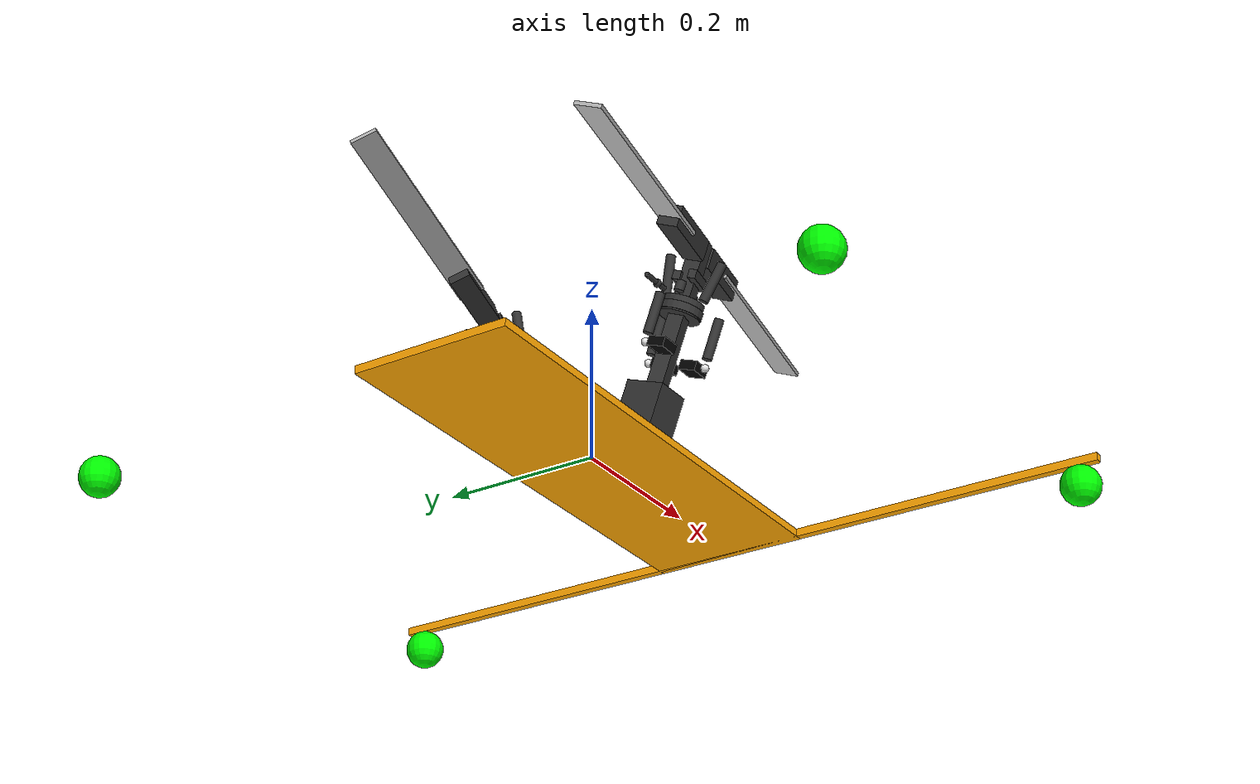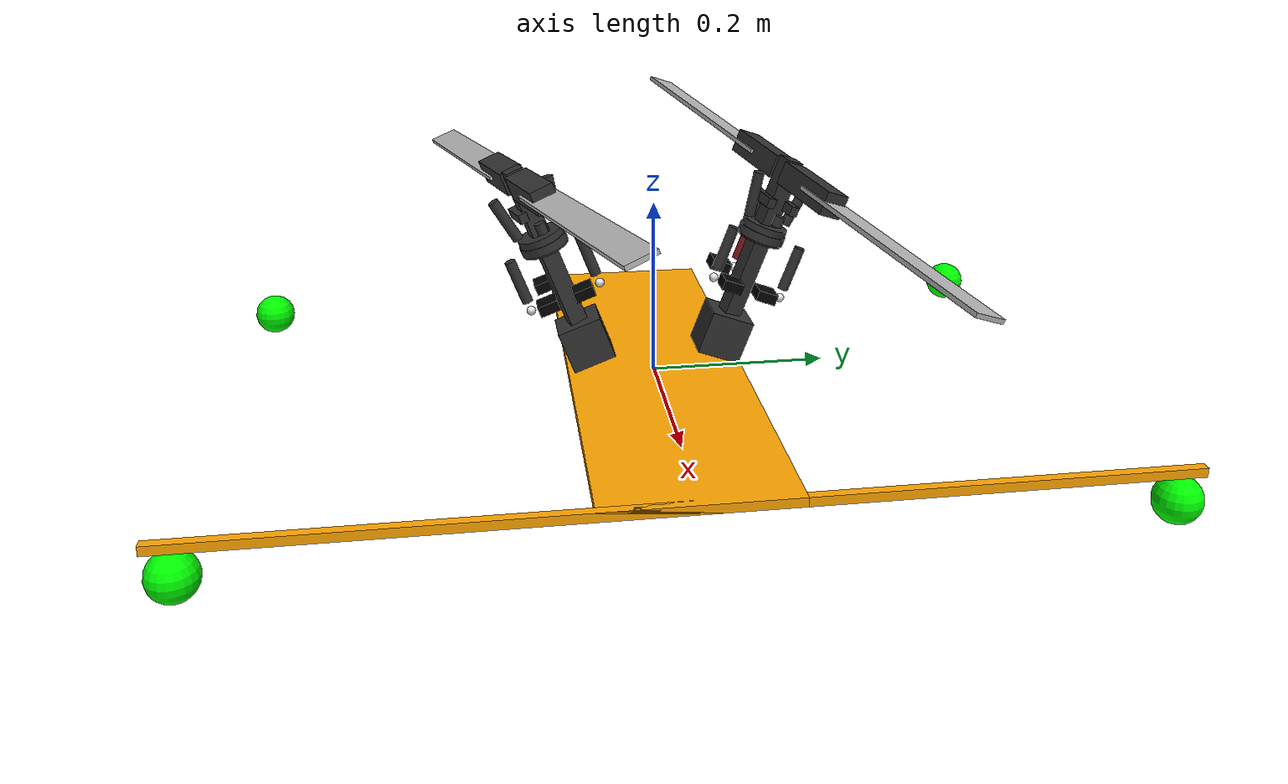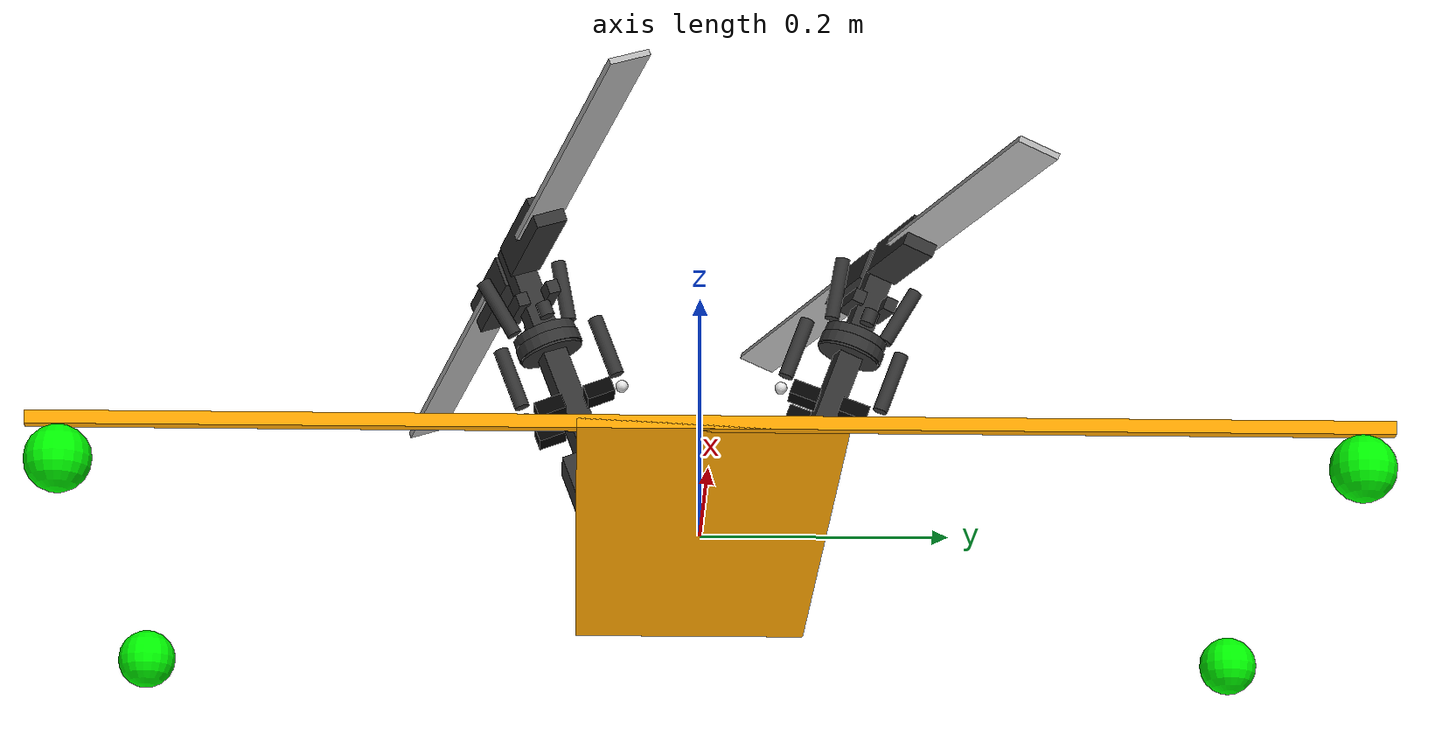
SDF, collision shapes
<?xml version="1.0"?>
<sdf version="1.9">
  <model name="helicopter_dual_intermesh">
    <link name="base_link">
      <inertial>
        <pose degrees="true">0 0 0 0 0 0</pose>
        <mass>1.0</mass>
        <inertia>
          <ixx>0.003341667</ixx>
          <ixy>0</ixy>
          <ixz>0</ixz>
          <iyy>0.035216667</iyy>
          <iyz>0</iyz>
          <izz>0.038541667</izz>
        </inertia>
      </inertial>
      <collision name="collision">
        <geometry>
          <box>
            <size>0.65 0.2 0.01</size>
          </box>
        </geometry>
      </collision>
      <collision name="collision_stab_1">
        <pose degrees="true">0.32 0 0 0 0 0</pose>
        <geometry>
          <box>
            <size>0.01 1.0 0.01</size>
          </box>
        </geometry>
      </collision>
      <collision name="collision_stab_2">
        <pose degrees="true">0.32 0 0 0 0 0</pose>
        <geometry>
          <box>
            <size>0.01 1.0 0.01</size>
          </box>
        </geometry>
      </collision>
      <visual name="visual">
        <geometry>
          <box>
            <size>0.65 0.2 0.01</size>
          </box>
        </geometry>
        <material>
          <ambient>1 0.65 0</ambient>
          <diffuse>1 0.65 0</diffuse>
          <specular>0.1 0.1 0.1</specular>
        </material>
      </visual>
      <visual name="visual_stab_1">
        <pose degrees="true">0.32 0 0 0 0 0</pose>
        <geometry>
          <box>
            <size>0.01 1.0 0.01</size>
          </box>
        </geometry>
        <material>
          <ambient>1 0.65 0</ambient>
          <diffuse>1 0.65 0</diffuse>
          <specular>0.1 0.1 0.1</specular>
        </material>
      </visual>
      <visual name="visual_stab_2">
        <pose degrees="true">-0.32 0 0 0 0 0</pose>
        <geometry>
          <box>
            <size>0.01 1.0 0.01</size>
          </box>
        </geometry>
        <material>
          <ambient>1 0.65 0</ambient>
          <diffuse>1 0.65 0</diffuse>
          <specular>0.1 0.1 0.1</specular>
        </material>
      </visual>

      <sensor name="imu_sensor" type="imu">
        <pose degrees="true">0.15 0 0 180 0 0</pose>
        <always_on>1</always_on>
        <update_rate>1000.0</update_rate>
      </sensor>
    </link>

    <include>
      <uri>model://rotor_head_cw</uri>
      <name>rotor_head_cw</name>
      <pose degrees="true">0 -0.15 0.23 20 -5 13</pose>
    </include>
    <joint name="rotor_head_cw_joint" type="fixed">
      <pose degrees="true">0 0 0 0 0 0</pose>
      <parent>base_link</parent>
      <child>rotor_head_cw::base_link</child>
    </joint>

    <include>
      <uri>model://rotor_head_ccw</uri>
      <name>rotor_head_ccw</name>
      <pose degrees="true">0 0.15 0.23 -20 5 13</pose>
    </include>
    <joint name="rotor_head_ccw_joint" type="fixed">
      <pose degrees="true">0 0 0 0 0 0</pose>
      <parent>base_link</parent>
      <child>rotor_head_ccw::base_link</child>
    </joint>

    <!-- stabiliser wheels -->
    <link name="wheel_1_link">
      <pose degrees="true">0.32 0.475 -0.03 0 0 0</pose>
      <inertial>
        <mass>0.05</mass>
        <inertia>
          <ixx>1.25000E-05</ixx>
          <ixy>0</ixy>
          <ixz>0</ixz>
          <iyy>1.25000E-05</iyy>
          <iyz>0</iyz>
          <izz>1.25000E-05</izz>
        </inertia>
      </inertial>
      <collision name="collision">
        <geometry>
          <sphere>
            <radius>0.025</radius>
          </sphere>
        </geometry>
        <surface>
          <friction>
            <ode>
              <mu>1.0e6</mu>
              <mu2>1.0e6</mu2>
            </ode>
          </friction>
        </surface>
      </collision>
      <visual name="visual">
        <geometry>
          <sphere>
            <radius>0.025</radius>
          </sphere>
        </geometry>
        <material>
          <ambient>0 1 0</ambient>
          <diffuse>0 1 0</diffuse>
          <specular>0.1 0.1 0.1 1</specular>
        </material>
      </visual>
    </link>
    <joint name="wheel_1_joint" type="fixed">
      <pose degrees="true">0 0 0 0 0 0</pose>
      <parent>base_link</parent>
      <child>wheel_1_link</child>
    </joint>

    <link name="wheel_2_link">
      <pose degrees="true">0.32 -0.475 -0.03 0 0 0</pose>
      <inertial>
        <mass>0.05</mass>
        <inertia>
          <ixx>1.25000E-05</ixx>
          <ixy>0</ixy>
          <ixz>0</ixz>
          <iyy>1.25000E-05</iyy>
          <iyz>0</iyz>
          <izz>1.25000E-05</izz>
        </inertia>
      </inertial>
      <collision name="collision">
        <geometry>
          <sphere>
            <radius>0.025</radius>
          </sphere>
        </geometry>
        <surface>
          <friction>
            <ode>
              <mu>1.0e6</mu>
              <mu2>1.0e6</mu2>
            </ode>
          </friction>
          </surface>
      </collision>
      <visual name="visual">
        <geometry>
          <sphere>
            <radius>0.025</radius>
          </sphere>
        </geometry>
        <material>
          <ambient>0 1 0</ambient>
          <diffuse>0 1 0</diffuse>
          <specular>0.1 0.1 0.1 1</specular>
        </material>
      </visual>
    </link>
    <joint name="wheel_2_joint" type="fixed">
      <pose degrees="true">0 0 0 0 0 0</pose>
      <parent>base_link</parent>
      <child>wheel_2_link</child>
    </joint>

    <link name="wheel_3_link">
      <pose degrees="true">-0.32 -0.475 -0.03 0 0 0</pose>
      <inertial>
        <mass>0.05</mass>
        <inertia>
          <ixx>1.25000E-05</ixx>
          <ixy>0</ixy>
          <ixz>0</ixz>
          <iyy>1.25000E-05</iyy>
          <iyz>0</iyz>
          <izz>1.25000E-05</izz>
        </inertia>
      </inertial>
      <collision name="collision">
        <geometry>
          <sphere>
            <radius>0.025</radius>
          </sphere>
        </geometry>
        <surface>
          <friction>
            <ode>
              <mu>1.0e6</mu>
              <mu2>1.0e6</mu2>
            </ode>
          </friction>
          </surface>
      </collision>
      <visual name="visual">
        <geometry>
          <sphere>
            <radius>0.025</radius>
          </sphere>
        </geometry>
        <material>
          <ambient>0 1 0</ambient>
          <diffuse>0 1 0</diffuse>
          <specular>0.1 0.1 0.1 1</specular>
        </material>
      </visual>
    </link>
    <joint name="wheel_3_joint" type="fixed">
      <pose degrees="true">0 0 0 0 0 0</pose>
      <parent>base_link</parent>
      <child>wheel_3_link</child>
    </joint>

    <link name="wheel_4_link">
      <pose degrees="true">-0.32 0.475 -0.03 0 0 0</pose>
      <inertial>
        <mass>0.05</mass>
        <inertia>
          <ixx>1.25000E-05</ixx>
          <ixy>0</ixy>
          <ixz>0</ixz>
          <iyy>1.25000E-05</iyy>
          <iyz>0</iyz>
          <izz>1.25000E-05</izz>
        </inertia>
      </inertial>
      <collision name="collision">
        <geometry>
          <sphere>
            <radius>0.025</radius>
          </sphere>
        </geometry>
        <surface>
          <friction>
            <ode>
              <mu>1.0e6</mu>
              <mu2>1.0e6</mu2>
            </ode>
          </friction>
          </surface>
      </collision>
      <visual name="visual">
        <geometry>
          <sphere>
            <radius>0.025</radius>
          </sphere>
        </geometry>
        <material>
          <ambient>0 1 0</ambient>
          <diffuse>0 1 0</diffuse>
          <specular>0.1 0.1 0.1 1</specular>
        </material>
      </visual>
    </link>
    <joint name="wheel_4_joint" type="fixed">
      <pose degrees="true">0 0 0 0 0 0</pose>
      <parent>base_link</parent>
      <child>wheel_4_link</child>
    </joint>

    <!-- plugins -->
    <plugin name="ArduPilotPlugin"
      filename="ArduPilotPlugin">
      <!-- Port settings -->
      <fdm_addr>127.0.0.1</fdm_addr>
      <fdm_port_in>9002</fdm_port_in>
      <connectionTimeoutMaxCount>5</connectionTimeoutMaxCount>
      <lock_step>1</lock_step>
      <have_32_channels>0</have_32_channels>

      <!-- Frame conventions
        Require by ArduPilot: change model and gazebo from XYZ to XY-Z coordinates
      -->
      <modelXYZToAirplaneXForwardZDown degrees="true">0 0 0 180 0 0</modelXYZToAirplaneXForwardZDown>
      <gazeboXYZToNED degrees="true">0 0 0 180 0 90</gazeboXYZToNED>

      <!-- Sensors -->
      <imuName>base_link::imu_sensor</imuName>

      <!--
        FRAME_CLASS      11 (Dual Heli)
        FRAME_TYPE       1 (X)
      -->

      <!--
        SERVO8_FUNCTION 31 (HeliRSC)
      -->
      <control channel="7">
        <jointName>rotor_head_ccw::main_joint</jointName>
        <multiplier>500</multiplier>
        <offset>0</offset>
        <servo_min>1000</servo_min>
        <servo_max>2000</servo_max>
        <type>COMMAND</type>
        <cmd_topic>/model/rotor_head_ccw/joint/main_joint/cmd_vel</cmd_topic>
      </control>

      <control channel="7">
        <jointName>rotor_head_cw::main_joint</jointName>
        <multiplier>500</multiplier>
        <offset>0</offset>
        <servo_min>1000</servo_min>
        <servo_max>2000</servo_max>
        <type>COMMAND</type>
        <cmd_topic>/model/rotor_head_cw/joint/main_joint/cmd_vel</cmd_topic>
      </control>

      <!--
        SERVO1_FUNCTION 33 (Motor1)
      -->
      <control channel="0">
        <jointName>rotor_head_ccw::servo_arm_1_joint</jointName>
        <multiplier>0.04</multiplier>
        <offset>-0.5</offset>
        <servo_max>2000</servo_max>
        <servo_min>1000</servo_min>
        <type>COMMAND</type>
        <cmd_topic>/model/rotor_head_ccw/joint/servo_arm_1_joint/0/cmd_pos</cmd_topic>
      </control>

      <!--
        SERVO2_FUNCTION 34 (Motor2)
      -->
      <control channel="1">
        <jointName>rotor_head_ccw::servo_arm_2_joint</jointName>
        <multiplier>0.04</multiplier>
        <offset>-0.5</offset>
        <servo_max>2000</servo_max>
        <servo_min>1000</servo_min>
        <type>COMMAND</type>
        <cmd_topic>/model/rotor_head_ccw/joint/servo_arm_2_joint/0/cmd_pos</cmd_topic>
      </control>

      <!--
        SERVO3_FUNCTION 35 (Motor3)
      -->
      <control channel="2">
        <jointName>rotor_head_ccw::servo_arm_3_joint</jointName>
        <multiplier>0.04</multiplier>
        <offset>-0.5</offset>
        <servo_max>2000</servo_max>
        <servo_min>1000</servo_min>
        <type>COMMAND</type>
        <cmd_topic>/model/rotor_head_ccw/joint/servo_arm_3_joint/0/cmd_pos</cmd_topic>
      </control>

      <!--
        SERVO4_FUNCTION 36 (Motor4)
      -->
      <control channel="3">
        <jointName>rotor_head_cw::servo_arm_1_joint</jointName>
        <multiplier>0.04</multiplier>
        <offset>-0.5</offset>
        <servo_max>2000</servo_max>
        <servo_min>1000</servo_min>
        <type>COMMAND</type>
        <cmd_topic>/model/rotor_head_cw/joint/servo_arm_1_joint/0/cmd_pos</cmd_topic>
      </control>

      <!--
        SERVO5_FUNCTION 37 (Motor5)
      -->
      <control channel="4">
        <jointName>rotor_head_cw::servo_arm_2_joint</jointName>
        <multiplier>0.04</multiplier>
        <offset>-0.5</offset>
        <servo_max>2000</servo_max>
        <servo_min>1000</servo_min>
        <type>COMMAND</type>
        <cmd_topic>/model/rotor_head_cw/joint/servo_arm_2_joint/0/cmd_pos</cmd_topic>
      </control>

      <!--
        SERVO6_FUNCTION 38 (Motor6)
      -->
      <control channel="5">
        <jointName>rotor_head_cw::servo_arm_3_joint</jointName>
        <multiplier>0.04</multiplier>
        <offset>-0.5</offset>
        <servo_max>2000</servo_max>
        <servo_min>1000</servo_min>
        <type>COMMAND</type>
        <cmd_topic>/model/rotor_head_cw/joint/servo_arm_3_joint/0/cmd_pos</cmd_topic>
      </control>

    </plugin>
  </model>

</sdf>

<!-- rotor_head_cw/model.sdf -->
<sdf version="1.11">
  <model name="rotor_head_cw">
    <link name="base_link">
      <pose degrees="true">0 0 -0.2 0 0 -13</pose>
      <inertial>
        <pose>0 0 0 0 0 0</pose>
        <mass>0.1</mass>
        <inertia>
          <ixx>4.16667E-05</ixx>
          <ixy>0</ixy>
          <ixz>0</ixz>
          <iyy>4.16667E-05</iyy>
          <iyz>0</iyz>
          <izz>4.16667E-05</izz>
        </inertia>
      </inertial>
      <collision name="collision">
        <geometry>
          <box>
            <size>0.05 0.05 0.05</size>
          </box>
        </geometry>
      </collision>
      <visual name="visual">
        <geometry>
          <box>
            <size>0.05 0.05 0.05</size>
          </box>
        </geometry>
        <material>
          <ambient>0.2 0.2 0.2</ambient>
          <diffuse>0.2 0.2 0.2</diffuse>
          <specular>0.1 0.1 0.1 1</specular>
        </material>
      </visual>

    </link>
    <joint name="main_joint" type="revolute">
      <pose degrees="true">0 0 0 0 180 0</pose>
      <parent>base_link</parent>
      <child>main_link</child>
      <axis>
        <xyz>0 0 1</xyz>
        <limit>
          <lower>-1.0e16</lower>
          <upper>1.0e16</upper>
        </limit>
        <dynamics>
          <damping>0.001</damping>
          <friction>0</friction>
        </dynamics>
      </axis>
      <!-- Disabled - impacts performance at high rate needed for analysis -->
    </joint>

    <!-- guide (prismatic) -->
    <link name="guide_h_link">
      <pose relative_to="servo_rod_3a_link" degrees="true">-0.01 0.003 0 0 0 0</pose>
      <inertial>
        <mass>0.001</mass>
        <inertia>
          <ixx>1.00000E-08</ixx>
          <ixy>0</ixy>
          <ixz>0</ixz>
          <iyy>1.00000E-08</iyy>
          <iyz>0</iyz>
          <izz>1.00000E-08</izz>
        </inertia>
      </inertial>
      <collision name="collision">
        <geometry>
          <sphere>
            <radius>0.005</radius>
          </sphere>
        </geometry>
      </collision>
      <visual name="visual">
        <geometry>
          <sphere>
            <radius>0.005</radius>
          </sphere>
        </geometry>
        <material>
          <ambient>0.2 0.2 0.2</ambient>
          <diffuse>0.2 0.2 0.2</diffuse>
          <specular>0.1 0.1 0.1 1</specular>
        </material>
      </visual>
    </link>
    <joint name="guide_h_joint" type="prismatic">
      <pose degrees="true">0 0 0 0 0 -13</pose>
      <parent>swash_plate_down_part_link</parent>
      <child>guide_h_link</child>
      <axis>
        <xyz>1 0 0</xyz>
        <limit>
          <lower>-0.05</lower>
          <upper>0.05</upper>
        </limit>
        <dynamics>
          <damping>0.01</damping>
          <friction>0</friction>
        </dynamics>
      </axis>
    </joint>
    <link name="guide_b_link">
      <pose relative_to="guide_h_link" degrees="true">0 0 0 0 0 0</pose>
      <inertial>
        <mass>0.01</mass>
        <inertia>
          <ixx>1.00000E-07</ixx>
          <ixy>0</ixy>
          <ixz>0</ixz>
          <iyy>1.00000E-07</iyy>
          <iyz>0</iyz>
          <izz>1.00000E-07</izz>
        </inertia>
      </inertial>
      <collision name="collision">
        <geometry>
          <sphere>
            <radius>0.005</radius>
          </sphere>
        </geometry>
      </collision>
      <visual name="visual">
        <geometry>
          <sphere>
            <radius>0.005</radius>
          </sphere>
        </geometry>
        <material>
          <ambient>0.2 0.2 0.2</ambient>
          <diffuse>0.2 0.2 0.2</diffuse>
          <specular>0.1 0.1 0.1 1</specular>
        </material>
      </visual>
    </link>
    <joint name="guide_b_joint" type="ball">
      <pose degrees="true">0 0 0 0 0 -13</pose>
      <parent>guide_h_link</parent>
      <child>guide_b_link</child>
      <axis>
        <dynamics>
          <damping>0.01</damping>
        </dynamics>
      </axis>
    </joint>
    <link name="guide_v_link">
      <pose relative_to="guide_b_link" degrees="true">0 0 0 0 0 0</pose>
      <inertial>
        <mass>0.01</mass>
        <inertia>
          <ixx>1.00000E-07</ixx>
          <ixy>0</ixy>
          <ixz>0</ixz>
          <iyy>1.00000E-07</iyy>
          <iyz>0</iyz>
          <izz>1.00000E-07</izz>
        </inertia>
      </inertial>
      <collision name="collision">
        <geometry>
          <sphere>
            <radius>0.005</radius>
          </sphere>
        </geometry>
      </collision>
      <visual name="visual">
        <geometry>
          <sphere>
            <radius>0.005</radius>
          </sphere>
        </geometry>
        <material>
          <ambient>0.2 0.2 0.2</ambient>
          <diffuse>0.2 0.2 0.2</diffuse>
          <specular>0.1 0.1 0.1 1</specular>
        </material>
      </visual>
    </link>
    <joint name="guide_v_joint" type="prismatic">
      <pose degrees="true">0 0 0 0 0 -13</pose>
      <parent>guide_b_link</parent>
      <child>guide_v_link</child>
      <axis>
        <xyz>0 0 1</xyz>
        <limit>
          <lower>-0.05</lower>
          <upper>0.05</upper>
        </limit>
        <dynamics>
          <damping>0.01</damping>
          <friction>0</friction>
        </dynamics>
      </axis>
    </joint>

    <!-- servos (prismatic) -->
    <link name="servo_3_link">
      <pose degrees="true">-0.045 -0.01 -0.135 0 90 -13</pose>
      <inertial>
        <pose>0 0 0 0 0 0</pose>
        <mass>0.015</mass>
        <inertia>
          <ixx>8.35513E-07</ixx>
          <ixy>0</ixy>
          <ixz>0</ixz>
          <iyy>1.48756E-06</iyy>
          <iyz>0</iyz>
          <izz>1.01205E-06</izz>
        </inertia>
      </inertial>
      <collision name="collision">
        <geometry>
          <box>
            <size>0.012 0.0229 0.0258</size>
          </box>
        </geometry>
      </collision>
      <visual name="visual">
        <geometry>
          <box>
            <size>0.012 0.0229 0.0258</size>
          </box>
        </geometry>
        <material>
          <ambient>0.01 0.01 0.01</ambient>
          <diffuse>0.01 0.01 0.01</diffuse>
          <specular>0.01 0.01 0.01</specular>
        </material>
      </visual>
    </link>
    <joint name="servo_3_joint" type="fixed">
      <pose degrees="true">0 0 0 0 0 0</pose>
      <parent>base_link</parent>
      <child>servo_3_link</child>
    </joint>
    <link name="servo_arm_3_link">
      <pose relative_to="servo_3_link" degrees="true">0.0 0.02 -0.005 0 0 0</pose>
      <inertial>
        <mass>0.001</mass>
        <inertia>
          <ixx>1.00000E-08</ixx>
          <ixy>0</ixy>
          <ixz>0</ixz>
          <iyy>1.00000E-08</iyy>
          <iyz>0</iyz>
          <izz>1.00000E-08</izz>
        </inertia>
      </inertial>
      <collision name="collision">
        <geometry>
          <sphere>
            <radius>0.005</radius>
          </sphere>
        </geometry>
      </collision>
      <visual name="visual">
        <geometry>
          <sphere>
            <radius>0.005</radius>
          </sphere>
        </geometry>
        <material>
          <ambient>0.9 0.9 0.9</ambient>
          <diffuse>0.9 0.9 0.9</diffuse>
          <specular>0.1 0.1 0.1 1</specular>
        </material>
      </visual>
    </link>
    <joint name="servo_arm_3_joint" type="prismatic">
      <pose degrees="true">0 0 0 0 0 180</pose>
      <parent>servo_3_link</parent>
      <child>servo_arm_3_link</child>
      <axis>
        <xyz>1 0 0</xyz>
        <limit>
          <lower>-0.02</lower>
          <upper>0.02</upper>
          <effort>1.0e7</effort>
        </limit>
        <dynamics>
          <damping>0.01</damping>
          <friction>0</friction>
        </dynamics>
      </axis>
    </joint>
    <link name="servo_rod_3b_link">
      <pose degrees="true">-0.045662 0.01084 -0.0651 0 0 0</pose>
      <inertial>
        <pose degrees="true">0 0 -0.03356 0 0 0</pose>
        <mass>0.010</mass>
        <inertia>
          <ixx>2.2575E-06</ixx>
          <ixy>0</ixy>
          <ixz>0</ixz>
          <iyy>2.2575E-06</iyy>
          <iyz>0</iyz>
          <izz>0.00000018</izz>
        </inertia>
      </inertial>
      <collision name="collision">
        <pose degrees="true">0 0 -0.03356 0 0 0</pose>
        <geometry>
          <cylinder>
            <length>0.051</length>
            <radius>0.006</radius>
          </cylinder>
        </geometry>
      </collision>
      <visual name="visual">
        <geometry>
          <mesh>
            <scale>1 1 1</scale>
            <uri>meshes/servo_rod.dae</uri>
          </mesh>
        </geometry>
        <material>
          <ambient>0.2 0.2 0.2</ambient>
          <diffuse>0.2 0.2 0.2</diffuse>
          <specular>0.1 0.1 0.1 1</specular>
        </material>
      </visual>
    </link>
    <joint name="servo_rod_3b_joint" type="ball">
      <pose relative_to="servo_arm_3_joint" degrees="true">0 0 0 0 0 0</pose>
      <parent>servo_arm_3_link</parent>
      <child>servo_rod_3b_link</child>
      <axis>
        <dynamics>
          <damping>0.01</damping>
        </dynamics>
      </axis>
    </joint>

    <link name="servo_2_link">
      <pose degrees="true">0.0145 -0.066 -0.135 0 90 -13</pose>
      <inertial>
        <pose>0 0.04 0 0 0 0</pose>
        <mass>0.015</mass>
        <inertia>
          <ixx>8.35513E-07</ixx>
          <ixy>0</ixy>
          <ixz>0</ixz>
          <iyy>1.48756E-06</iyy>
          <iyz>0</iyz>
          <izz>1.01205E-06</izz>
        </inertia>
      </inertial>
      <collision name="collision">
        <pose degrees="true">0 0.04 0 0 0 0</pose>
        <geometry>
          <box>
            <size>0.012 0.0229 0.0258</size>
          </box>
        </geometry>
      </collision>
      <visual name="visual">
        <pose degrees="true">0 0.04 0 0 0 0</pose>
        <geometry>
          <box>
            <size>0.012 0.0229 0.0258</size>
          </box>
        </geometry>
        <material>
          <ambient>0.01 0.01 0.01</ambient>
          <diffuse>0.01 0.01 0.01</diffuse>
          <specular>0.01 0.01 0.01</specular>
        </material>
      </visual>
    </link>
    <joint name="servo_2_joint" type="fixed">
      <pose degrees="true">0 0 0 0 0 0</pose>
      <parent>base_link</parent>
      <child>servo_2_link</child>
    </joint>
    <link name="servo_arm_2_link">
      <pose relative_to="servo_2_link" degrees="true">0.0 0.020 -0.005 0 0 0</pose>
      <inertial>
        <mass>0.001</mass>
        <inertia>
          <ixx>1.00000E-08</ixx>
          <ixy>0</ixy>
          <ixz>0</ixz>
          <iyy>1.00000E-08</iyy>
          <iyz>0</iyz>
          <izz>1.00000E-08</izz>
        </inertia>
      </inertial>
      <collision name="collision">
        <geometry>
          <sphere>
            <radius>0.005</radius>
          </sphere>
        </geometry>
      </collision>
      <visual name="visual">
        <geometry>
          <sphere>
            <radius>0.005</radius>
          </sphere>
        </geometry>
        <material>
          <ambient>0.9 0.9 0.9</ambient>
          <diffuse>0.9 0.9 0.9</diffuse>
          <specular>0.1 0.1 0.1 1</specular>
        </material>
      </visual>
    </link>
    <joint name="servo_arm_2_joint" type="prismatic">
      <pose degrees="true">0 0 0 0 0 180</pose>
      <parent>servo_2_link</parent>
      <child>servo_arm_2_link</child>
      <axis>
        <xyz>1 0 0</xyz>
        <limit>
          <lower>-0.02</lower>
          <upper>0.02</upper>
          <effort>1.0e7</effort>
        </limit>
        <dynamics>
          <damping>0.01</damping>
          <friction>0</friction>
        </dynamics>
      </axis>
    </joint>
    <link name="servo_rod_2b_link">
      <pose degrees="true">0.01343 -0.04493 -0.0651 0 0 0</pose>
      <inertial>
        <pose degrees="true">0 0 -0.03356 0 0 0</pose>
        <mass>0.010</mass>
        <inertia>
          <ixx>2.2575E-06</ixx>
          <ixy>0</ixy>
          <ixz>0</ixz>
          <iyy>2.2575E-06</iyy>
          <iyz>0</iyz>
          <izz>0.00000018</izz>
        </inertia>
      </inertial>
      <collision name="collision">
        <pose degrees="true">0 0 -0.03356 0 0 0</pose>
        <geometry>
          <cylinder>
            <length>0.051</length>
            <radius>0.006</radius>
          </cylinder>
        </geometry>
      </collision>
      <visual name="visual">
        <geometry>
          <mesh>
            <scale>1 1 1</scale>
            <uri>meshes/servo_rod.dae</uri>
          </mesh>
        </geometry>
        <material>
          <ambient>0.2 0.2 0.2</ambient>
          <diffuse>0.2 0.2 0.2</diffuse>
          <specular>0.1 0.1 0.1 1</specular>
        </material>
      </visual>
    </link>
    <joint name="servo_rod_2b_joint" type="ball">
      <pose relative_to="servo_arm_2_joint" degrees="true">0 0 0 0 0 0</pose>
      <parent>servo_arm_2_link</parent>
      <child>servo_rod_2b_link</child>
      <axis>
        <dynamics>
          <damping>0.01</damping>
        </dynamics>
      </axis>
    </joint>

    <link name="servo_1_link">
      <pose degrees="true">0.0335 0.0135 -0.135 0 90 -13</pose>
      <inertial>
        <pose>0 0 0 0 0 0</pose>
        <mass>0.015</mass>
        <inertia>
          <ixx>8.35513E-07</ixx>
          <ixy>0</ixy>
          <ixz>0</ixz>
          <iyy>1.48756E-06</iyy>
          <iyz>0</iyz>
          <izz>1.01205E-06</izz>
        </inertia>
      </inertial>
      <collision name="collision">
        <geometry>
          <box>
            <size>0.012 0.0229 0.0258</size>
          </box>
        </geometry>
      </collision>
      <visual name="visual">
        <geometry>
          <box>
            <size>0.012 0.0229 0.0258</size>
          </box>
        </geometry>
        <material>
          <ambient>0.01 0.01 0.01</ambient>
          <diffuse>0.01 0.01 0.01</diffuse>
          <specular>0.01 0.01 0.01</specular>
        </material>
      </visual>
    </link>
    <joint name="servo_1_joint" type="fixed">
      <pose degrees="true">0 0 0 0 0 0</pose>
      <parent>base_link</parent>
      <child>servo_1_link</child>
    </joint>
    <link name="servo_arm_1_link">
      <pose relative_to="servo_1_link" degrees="true">0.0 0.02 -0.005 0 0 0</pose>
      <inertial>
        <mass>0.001</mass>
        <inertia>
          <ixx>1.00000E-08</ixx>
          <ixy>0</ixy>
          <ixz>0</ixz>
          <iyy>1.00000E-08</iyy>
          <iyz>0</iyz>
          <izz>1.00000E-08</izz>
        </inertia>
      </inertial>
      <collision name="collision">
        <geometry>
          <sphere>
            <radius>0.005</radius>
          </sphere>
        </geometry>
      </collision>
      <visual name="visual">
        <geometry>
          <sphere>
            <radius>0.005</radius>
          </sphere>
        </geometry>
        <material>
          <ambient>0.9 0.9 0.9</ambient>
          <diffuse>0.9 0.9 0.9</diffuse>
          <specular>0.1 0.1 0.1 1</specular>
        </material>
      </visual>
    </link>
    <joint name="servo_arm_1_joint" type="prismatic">
      <pose degrees="true">0 0 0 0 0 180</pose>
      <parent>servo_1_link</parent>
      <child>servo_arm_1_link</child>
      <axis>
        <xyz>1 0 0</xyz>
        <limit>
          <lower>-0.02</lower>
          <upper>0.02</upper>
          <effort>1.0e7</effort>
        </limit>
        <dynamics>
          <damping>0.01</damping>
          <friction>0</friction>
        </dynamics>
      </axis>
    </joint>
    <link name="servo_rod_1b_link">
      <pose degrees="true">0.03219 0.03409 -0.0651 0 0 0</pose>
      <inertial>
        <pose degrees="true">0 0 -0.03356 0 0 0</pose>
        <mass>0.010</mass>
        <inertia>
          <ixx>2.2575E-06</ixx>
          <ixy>0</ixy>
          <ixz>0</ixz>
          <iyy>2.2575E-06</iyy>
          <iyz>0</iyz>
          <izz>0.00000018</izz>
        </inertia>
      </inertial>
      <collision name="collision">
        <pose degrees="true">0 0 -0.03356 0 0 0</pose>
        <geometry>
          <cylinder>
            <length>0.051</length>
            <radius>0.006</radius>
          </cylinder>
        </geometry>
      </collision>
      <visual name="visual">
        <geometry>
          <mesh>
            <scale>1 1 1</scale>
            <uri>meshes/servo_rod.dae</uri>
          </mesh>
        </geometry>
        <material>
          <ambient>0.2 0.2 0.2</ambient>
          <diffuse>0.2 0.2 0.2</diffuse>
          <specular>0.1 0.1 0.1 1</specular>
        </material>
      </visual>
    </link>
    <joint name="servo_rod_1b_joint" type="ball">
      <pose relative_to="servo_arm_1_joint" degrees="true">0 0 0 0 0 0</pose>
      <parent>servo_arm_1_link</parent>
      <child>servo_rod_1b_link</child>
      <axis>
        <dynamics>
          <damping>0.01</damping>
        </dynamics>
      </axis>
    </joint>

    <!-- rotor head -->
    <link name="main_link">
      <inertial>
        <pose>0 0 -0.1 0 0 0</pose>
        <mass>0.10</mass>
        <inertia>
          <ixx>0.000444167</ixx>
          <ixy>0</ixy>
          <ixz>0</ixz>
          <iyy>0.000444167</iyy>
          <iyz>0</iyz>
          <izz>6.66667E-06</izz>
        </inertia>
      </inertial>
      <collision name="collision">
        <pose>0 0 -0.1 0 0 0</pose>
        <geometry>
          <box>
            <size>0.02 0.02 0.23</size>
          </box>
        </geometry>
      </collision>
      <visual name="visual_main_body">
        <geometry>
          <mesh>
            <scale>1 1 1</scale>
            <uri>meshes/rotor_head_cw.dae</uri>
            <submesh>
              <name>main_body</name>
            </submesh>
          </mesh>
        </geometry>
        <material>
          <ambient>0.2 0.2 0.2</ambient>
          <diffuse>0.2 0.2 0.2</diffuse>
          <specular>0.1 0.1 0.1 1</specular>
        </material>
      </visual>
    </link>

    <link name="blade_grip_1_link">
      <inertial>
        <pose degrees="true">-0.06 0 0 0 0 0</pose>
        <mass>0.10</mass>
        <inertia>
          <ixx>1.12667E-05</ixx>
          <ixy>0</ixy>
          <ixz>0</ixz>
          <iyy>8.89667E-05</iyy>
          <iyz>0</iyz>
          <izz>8.89667E-05</izz>
        </inertia>
      </inertial>
      <collision name="collision">
        <pose degrees="true">-0.06 0 0 0 0 0</pose>
        <geometry>
          <box>
            <size>0.1 0.026 0.026</size>
          </box>
        </geometry>
      </collision>
      <visual name="visual">
        <geometry>
          <mesh>
            <scale>1 1 1</scale>
            <uri>meshes/rotor_head_cw.dae</uri>
            <submesh>
              <name>blade_grip_1</name>
            </submesh>
          </mesh>
        </geometry>
        <material>
          <ambient>0.2 0.2 0.2</ambient>
          <diffuse>0.2 0.2 0.2</diffuse>
          <specular>0.1 0.1 0.1 1</specular>
        </material>
      </visual>
    </link>
    <joint name="blade_grip_1_joint" type="revolute">
      <pose degrees="true">-0.031 0 0 0 0 0</pose>
      <parent>main_link</parent>
      <child>blade_grip_1_link</child>
      <axis>
        <xyz>1 0 0</xyz>
        <limit>
          <lower>-1.570796</lower>
          <upper>1.570796</upper>
        </limit>
        <dynamics>
          <damping>0.01</damping>
          <friction>0</friction>
        </dynamics>
      </axis>
    </joint>

    <link name="blade_grip_2_link">
      <inertial>
        <pose degrees="true">0.06 0 0 0 0 180</pose>
        <mass>0.10</mass>
        <inertia>
          <ixx>1.12667E-05</ixx>
          <ixy>0</ixy>
          <ixz>0</ixz>
          <iyy>8.89667E-05</iyy>
          <iyz>0</iyz>
          <izz>8.89667E-05</izz>
        </inertia>
      </inertial>
      <collision name="collision">
        <pose degrees="true">0.06 0 0 0 0 0</pose>
        <geometry>
          <box>
            <size>0.1 0.026 0.026</size>
          </box>
        </geometry>
      </collision>
      <visual name="visual">
        <geometry>
          <mesh>
            <scale>1 1 1</scale>
            <uri>meshes/rotor_head_cw.dae</uri>
            <submesh>
              <name>blade_grip_2</name>
            </submesh>
          </mesh>
        </geometry>
        <material>
          <ambient>0.2 0.2 0.2</ambient>
          <diffuse>0.2 0.2 0.2</diffuse>
          <specular>0.1 0.1 0.1 1</specular>
        </material>
      </visual>
    </link>
    <joint name="blade_grip_2_joint" type="revolute">
      <pose degrees="true">0.031 0 0 0 0 180</pose>
      <parent>main_link</parent>
      <child>blade_grip_2_link</child>
      <axis>
        <xyz>1 0 0</xyz>
        <limit>
          <lower>-1.570796</lower>
          <upper>1.570796</upper>
        </limit>
        <dynamics>
          <damping>0.01</damping>
          <friction>0</friction>
        </dynamics>
      </axis>
    </joint>

    <link name="lever_1_link">
      <inertial>
        <pose degrees="true">0.006 0.012 -0.036 0 0 0</pose>
        <mass>0.010</mass>
        <inertia>
          <ixx>1.84167E-07</ixx>
          <ixy>0</ixy>
          <ixz>0</ixz>
          <iyy>1.64167E-06</iyy>
          <iyz>0</iyz>
          <izz>1.62417E-06</izz>
        </inertia>
      </inertial>
      <collision name="collision">
        <pose degrees="true">0.006 0.012 -0.036 0 0 0</pose>
        <geometry>
          <box>
            <size>0.043 0.01 0.011</size>
          </box>
        </geometry>
      </collision>
      <visual name="visual">
        <geometry>
          <mesh>
            <scale>1 1 1</scale>
            <uri>meshes/rotor_head_cw.dae</uri>
            <submesh>
              <name>lever_1</name>
            </submesh>
          </mesh>
        </geometry>
        <material>
          <ambient>0.2 0.2 0.2</ambient>
          <diffuse>0.2 0.2 0.2</diffuse>
          <specular>0.1 0.1 0.1 1</specular>
        </material>
      </visual>
    </link>
    <joint name="lever_1_joint" type="revolute">
      <pose degrees="true">-0.00949 0.012 -0.036 0 0 0</pose>
      <parent>main_link</parent>
      <child>lever_1_link</child>
      <axis>
        <xyz>0 1 0</xyz>
        <limit>
          <lower>-1.570796</lower>
          <upper>1.570796</upper>
        </limit>
        <dynamics>
          <damping>0.01</damping>
          <friction>0</friction>
        </dynamics>
      </axis>
    </joint>

    <link name="lever_2_link">
      <inertial>
        <pose degrees="true">-0.006 -0.012 -0.036 0 0 180</pose>
        <mass>0.010</mass>
        <inertia>
          <ixx>1.84167E-07</ixx>
          <ixy>0</ixy>
          <ixz>0</ixz>
          <iyy>1.64167E-06</iyy>
          <iyz>0</iyz>
          <izz>1.62417E-06</izz>
        </inertia>
      </inertial>
      <collision name="collision">
        <pose degrees="true">-0.006 -0.012 -0.036 0 0 180</pose>
        <geometry>
          <box>
            <size>0.043 0.01 0.011</size>
          </box>
        </geometry>
      </collision>
      <visual name="visual">
        <geometry>
          <mesh>
            <scale>1 1 1</scale>
            <uri>meshes/rotor_head_cw.dae</uri>
            <submesh>
              <name>lever_2</name>
            </submesh>
          </mesh>
        </geometry>
        <material>
          <ambient>0.2 0.2 0.2</ambient>
          <diffuse>0.2 0.2 0.2</diffuse>
          <specular>0.1 0.1 0.1 1</specular>
        </material>
      </visual>
    </link>
    <joint name="lever_2_joint" type="revolute">
      <pose degrees="true">0.00949 -0.012 -0.036 0 0 180</pose>
      <parent>main_link</parent>
      <child>lever_2_link</child>
      <axis>
        <xyz>0 1 0</xyz>
        <limit>
          <lower>-1.570796</lower>
          <upper>1.570796</upper>
        </limit>
        <dynamics>
          <damping>0.01</damping>
          <friction>0</friction>
        </dynamics>
      </axis>
    </joint>

    <link name="swash_plate_bearing_link">
      <inertial>
        <pose degrees="true">0 0 -0.0696 0 0 0</pose>
        <mass>0.01</mass>
        <inertia>
          <ixx>2.85833E-07</ixx>
          <ixy>0</ixy>
          <ixz>0</ixz>
          <iyy>2.85833E-07</iyy>
          <iyz>0</iyz>
          <izz>0.000000405</izz>
        </inertia>
      </inertial>
      <collision name="collision">
        <pose degrees="true">0 0 -0.0696 0 0 0</pose>
        <geometry>
          <cylinder>
            <length>0.01</length>
            <radius>0.009</radius>
          </cylinder>
        </geometry>
      </collision>
      <visual name="visual">
        <geometry>
          <mesh>
            <scale>1 1 1</scale>
            <uri>meshes/rotor_head_cw.dae</uri>
            <submesh>
              <name>swash_plate_bearing</name>
            </submesh>
          </mesh>
        </geometry>
        <material>
          <ambient>0.2 0.2 0.2</ambient>
          <diffuse>0.2 0.2 0.2</diffuse>
          <specular>0.1 0.1 0.1 1</specular>
        </material>
      </visual>
    </link>
    <joint name="swash_plate_bearing_joint" type="prismatic">
      <pose degrees="true">0 0 -0.068 0 0 0</pose>
      <parent>main_link</parent>
      <child>swash_plate_bearing_link</child>
      <axis>
        <xyz>0 0 1</xyz>
        <limit>
          <lower>-0.05</lower>
          <upper>0.05</upper>
        </limit>
        <dynamics>
          <damping>0.01</damping>
          <friction>0</friction>
        </dynamics>
      </axis>
    </joint>

    <link name="swash_plate_up_part_link">
      <inertial>
        <pose degrees="true">0 0 -0.073 0 0 0</pose>
        <mass>0.03</mass>
        <inertia>
          <ixx>0.00000607</ixx>
          <ixy>0</ixy>
          <ixz>0</ixz>
          <iyy>0.00000607</iyy>
          <iyz>0</iyz>
          <izz>0.00001014</izz>
        </inertia>
      </inertial>
      <collision name="collision">
        <pose degrees="true">0 0 -0.073 0 0 0</pose>
        <geometry>
          <cylinder>
            <length>0.02</length>
            <radius>0.026</radius>
          </cylinder>
        </geometry>
      </collision>
      <visual name="visual">
        <geometry>
          <mesh>
            <scale>1 1 1</scale>
            <uri>meshes/rotor_head_cw.dae</uri>
            <submesh>
              <name>swash_plate_up_part</name>
            </submesh>
          </mesh>
        </geometry>
        <material>
          <ambient>0.2 0.2 0.2</ambient>
          <diffuse>0.2 0.2 0.2</diffuse>
          <specular>0.1 0.1 0.1 1</specular>
        </material>
      </visual>
    </link>
    <joint name="swash_plate_up_part_joint" type="ball">
      <pose degrees="true">0 0 -0.068 0 0 0</pose>
      <parent>swash_plate_bearing_link</parent>
      <child>swash_plate_up_part_link</child>
      <axis>
        <dynamics>
          <damping>0.01</damping>
        </dynamics>
      </axis>
    </joint>

    <link name="swash_plate_down_part_link">
      <inertial>
        <pose degrees="true">0 0 -0.076 0 0 0</pose>
        <mass>0.03</mass>
        <inertia>
          <ixx>5.7175E-06</ixx>
          <ixy>0</ixy>
          <ixz>0</ixz>
          <iyy>5.7175E-06</iyy>
          <iyz>0</iyz>
          <izz>0.000010935</izz>
        </inertia>
      </inertial>
      <collision name="collision">
        <pose degrees="true">0 0 -0.076 0 0 0</pose>
        <geometry>
          <cylinder>
            <length>0.01</length>
            <radius>0.027</radius>
          </cylinder>
        </geometry>
      </collision>

      <collision name="collision_guide_rod">
        <pose degrees="true">-0.060662 0.0145 -0.0651 0 90 -13</pose>
        <geometry>
          <cylinder>
            <length>0.04</length>
            <radius>0.003</radius>
          </cylinder>
        </geometry>
      </collision>
      <visual name="visual_guide_rod">
        <pose degrees="true">-0.060662 0.0145 -0.0651 0 90 -13</pose>
        <geometry>
          <cylinder>
            <length>0.04</length>
            <radius>0.003</radius>
          </cylinder>
        </geometry>
        <material>
          <ambient>0.2 0.2 0.2</ambient>
          <diffuse>0.2 0.2 0.2</diffuse>
          <specular>0.1 0.1 0.1 1</specular>
        </material>
      </visual>

      <visual name="visual">
        <geometry>
          <mesh>
            <scale>1 1 1</scale>
            <uri>meshes/rotor_head_cw.dae</uri>
            <submesh>
              <name>swash_plate_down_part</name>
            </submesh>
          </mesh>
        </geometry>
        <material>
          <ambient>0.2 0.2 0.2</ambient>
          <diffuse>0.2 0.2 0.2</diffuse>
          <specular>0.1 0.1 0.1 1</specular>
        </material>
      </visual>
    </link>
    <joint name="swash_plate_down_part_joint" type="revolute">
      <pose degrees="true">0 0 -0.068 0 0 0</pose>
      <parent>swash_plate_up_part_link</parent>
      <child>swash_plate_down_part_link</child>
      <axis>
        <xyz>0 0 1</xyz>
        <limit>
          <lower>-1.0e16</lower>
          <upper>1.0e16</upper>
        </limit>
        <dynamics>
          <damping>0.001</damping>
          <friction>0</friction>
        </dynamics>
      </axis>
    </joint>

    <link name="blade_rod_1a_link">
      <inertial>
        <pose degrees="true">0 0.02875 -0.03356 -10.3 0 0</pose>
        <mass>0.010</mass>
        <inertia>
          <ixx>2.2575E-06</ixx>
          <ixy>0</ixy>
          <ixz>0</ixz>
          <iyy>2.2575E-06</iyy>
          <iyz>0</iyz>
          <izz>0.00000018</izz>
        </inertia>
      </inertial>
      <collision name="collision">
        <pose degrees="true">0 0.02875 -0.03356 -10.3 0 0</pose>
        <geometry>
          <cylinder>
            <length>0.051</length>
            <radius>0.006</radius>
          </cylinder>
        </geometry>
      </collision>
      <visual name="visual">
        <geometry>
          <mesh>
            <scale>1 1 1</scale>
            <uri>meshes/rotor_head_cw.dae</uri>
            <submesh>
              <name>blade_coupling_1</name>
            </submesh>
          </mesh>
        </geometry>
        <material>
          <ambient>0.2 0.2 0.2</ambient>
          <diffuse>0.2 0.2 0.2</diffuse>
          <specular>0.1 0.1 0.1 1</specular>
        </material>
      </visual>
    </link>
    <joint name="blade_rod_1a_joint" type="ball">
      <pose degrees="true">0 0.0349 0.000880 0 0 0</pose>
      <parent>blade_grip_1_link</parent>
      <child>blade_rod_1a_link</child>
      <axis>
        <dynamics>
          <damping>0.01</damping>
        </dynamics>
      </axis>
    </joint>

    <link name="blade_rod_1b_link">
      <inertial>
        <pose degrees="true">0 0.02875 -0.03356 -10.3 0 0</pose>
        <mass>0.010</mass>
        <inertia>
          <ixx>2.2575E-06</ixx>
          <ixy>0</ixy>
          <ixz>0</ixz>
          <iyy>2.2575E-06</iyy>
          <iyz>0</iyz>
          <izz>0.00000018</izz>
        </inertia>
      </inertial>
      <collision name="collision">
        <pose degrees="true">0 0.02875 -0.03356 -10.3 0 0</pose>
        <geometry>
          <cylinder>
            <length>0.051</length>
            <radius>0.006</radius>
          </cylinder>
        </geometry>
      </collision>
      <visual name="visual">
        <geometry>
          <mesh>
            <scale>1 1 1</scale>
            <uri>meshes/rotor_head_cw.dae</uri>
            <submesh>
              <name>blade_coupling_1</name>
            </submesh>
          </mesh>
        </geometry>
        <material>
          <ambient>0.2 0.2 0.2</ambient>
          <diffuse>0.2 0.2 0.2</diffuse>
          <specular>0.1 0.1 0.1 1</specular>
        </material>
      </visual>
    </link>
    <joint name="blade_rod_1b_joint" type="ball">
      <pose degrees="true">0 0.02252 -0.068 0 0 0</pose>
      <parent>swash_plate_up_part_link</parent>
      <child>blade_rod_1b_link</child>
      <axis>
        <dynamics>
          <damping>0.01</damping>
        </dynamics>
      </axis>
    </joint>

    <link name="blade_rod_2a_link">
      <inertial>
        <pose degrees="true">0 -0.02875 -0.03356 10.3 0 0</pose>
        <mass>0.010</mass>
        <inertia>
          <ixx>2.2575E-06</ixx>
          <ixy>0</ixy>
          <ixz>0</ixz>
          <iyy>2.2575E-06</iyy>
          <iyz>0</iyz>
          <izz>0.00000018</izz>
        </inertia>
      </inertial>
      <collision name="collision">
        <pose degrees="true">0 -0.02875 -0.03356 10.3 0 0</pose>
        <geometry>
          <cylinder>
            <length>0.051</length>
            <radius>0.006</radius>
          </cylinder>
        </geometry>
      </collision>
      <visual name="visual">
        <geometry>
          <mesh>
            <scale>1 1 1</scale>
            <uri>meshes/rotor_head_cw.dae</uri>
            <submesh>
              <name>blade_coupling_2</name>
            </submesh>
          </mesh>
        </geometry>
        <material>
          <ambient>0.2 0.2 0.2</ambient>
          <diffuse>0.2 0.2 0.2</diffuse>
          <specular>0.1 0.1 0.1 1</specular>
        </material>
      </visual>
    </link>
    <joint name="blade_rod_2a_joint" type="ball">
      <pose degrees="true">0 -0.0349 0.000880 0 0 180</pose>
      <parent>blade_grip_2_link</parent>
      <child>blade_rod_2a_link</child>
      <axis>
        <dynamics>
          <damping>0.01</damping>
        </dynamics>
      </axis>
    </joint>

    <link name="blade_rod_2b_link">
      <inertial>
        <pose degrees="true">0 -0.02875 -0.03356 10.3 0 0</pose>
        <mass>0.010</mass>
        <inertia>
          <ixx>2.2575E-06</ixx>
          <ixy>0</ixy>
          <ixz>0</ixz>
          <iyy>2.2575E-06</iyy>
          <iyz>0</iyz>
          <izz>0.00000018</izz>
        </inertia>
      </inertial>
      <collision name="collision">
        <pose degrees="true">0 -0.02875 -0.03356 10.3 0 0</pose>
        <geometry>
          <cylinder>
            <length>0.051</length>
            <radius>0.006</radius>
          </cylinder>
        </geometry>
      </collision>
      <visual name="visual">
        <geometry>
          <mesh>
            <scale>1 1 1</scale>
            <uri>meshes/rotor_head_cw.dae</uri>
            <submesh>
              <name>blade_coupling_2</name>
            </submesh>
          </mesh>
        </geometry>
        <material>
          <ambient>0.2 0.2 0.2</ambient>
          <diffuse>0.2 0.2 0.2</diffuse>
          <specular>0.1 0.1 0.1 1</specular>
        </material>
      </visual>
    </link>
    <joint name="blade_rod_2b_joint" type="ball">
      <pose degrees="true">0 -0.02252 -0.068 0 0 0</pose>
      <parent>swash_plate_up_part_link</parent>
      <child>blade_rod_2b_link</child>
      <axis>
        <dynamics>
          <damping>0.01</damping>
        </dynamics>
      </axis>
    </joint>

    <link name="lever_rod_1a_link">
      <inertial>
        <pose degrees="true">0.02251 0 -0.052 0 0 0</pose>
        <mass>0.010</mass>
        <inertia>
          <ixx>0.00000021</ixx>
          <ixy>0</ixy>
          <ixz>0</ixz>
          <iyy>0.00000021</iyy>
          <iyz>0</iyz>
          <izz>0.00000018</izz>
        </inertia>
      </inertial>
      <collision name="collision">
        <pose degrees="true">0.02251 0 -0.052 0 0 0</pose>
        <geometry>
          <cylinder>
            <length>0.012</length>
            <radius>0.006</radius>
          </cylinder>
        </geometry>
      </collision>
      <visual name="visual">
        <geometry>
          <mesh>
            <scale>1 1 1</scale>
            <uri>meshes/rotor_head_cw.dae</uri>
            <submesh>
              <name>lever_coupling_1</name>
            </submesh>
          </mesh>
        </geometry>
        <material>
          <ambient>0.2 0.2 0.2</ambient>
          <diffuse>0.2 0.2 0.2</diffuse>
          <specular>0.1 0.1 0.1 1</specular>
        </material>
      </visual>
    </link>
    <joint name="lever_rod_1a_joint" type="revolute">
      <pose degrees="true">0.02251 0 -0.036 0 0 0</pose>
      <parent>lever_1_link</parent>
      <child>lever_rod_1a_link</child>
      <axis>
        <xyz>0 1 0</xyz>
        <limit>
          <lower>-3.14159265</lower>
          <upper>3.14159265</upper>
        </limit>
        <dynamics>
          <damping>0.01</damping>
          <friction>0</friction>
        </dynamics>
      </axis>
    </joint>

    <link name="lever_rod_2a_link">
      <inertial>
        <pose degrees="true">-0.02251 0 -0.052 0 0 0</pose>
        <mass>0.010</mass>
        <inertia>
          <ixx>0.00000021</ixx>
          <ixy>0</ixy>
          <ixz>0</ixz>
          <iyy>0.00000021</iyy>
          <iyz>0</iyz>
          <izz>0.00000018</izz>
        </inertia>
      </inertial>
      <collision name="collision">
        <pose degrees="true">-0.02251 0 -0.052 0 0 0</pose>
        <geometry>
          <cylinder>
            <length>0.012</length>
            <radius>0.006</radius>
          </cylinder>
        </geometry>
      </collision>
      <visual name="visual">
        <geometry>
          <mesh>
            <scale>1 1 1</scale>
            <uri>meshes/rotor_head_cw.dae</uri>
            <submesh>
              <name>lever_coupling_2</name>
            </submesh>
          </mesh>
        </geometry>
        <material>
          <ambient>0.2 0.2 0.2</ambient>
          <diffuse>0.2 0.2 0.2</diffuse>
          <specular>0.1 0.1 0.1 1</specular>
        </material>
      </visual>
    </link>
    <joint name="lever_rod_2a_joint" type="revolute">
      <pose degrees="true">-0.02251 0 -0.036 0 0 180</pose>
      <parent>lever_2_link</parent>
      <child>lever_rod_2a_link</child>
      <axis>
        <xyz>0 1 0</xyz>
        <limit>
          <lower>-3.14159265</lower>
          <upper>3.14159265</upper>
        </limit>
        <dynamics>
          <damping>0.01</damping>
          <friction>0</friction>
        </dynamics>
      </axis>
    </joint>

    <link name="lever_rod_1b_link">
      <inertial>
        <pose degrees="true">0.02251 0 -0.052 0 0 0</pose>
        <mass>0.010</mass>
        <inertia>
          <ixx>0.00000021</ixx>
          <ixy>0</ixy>
          <ixz>0</ixz>
          <iyy>0.00000021</iyy>
          <iyz>0</iyz>
          <izz>0.00000018</izz>
        </inertia>
      </inertial>
      <collision name="collision">
        <pose degrees="true">0.02251 0 -0.052 0 0 0</pose>
        <geometry>
          <cylinder>
            <length>0.012</length>
            <radius>0.006</radius>
          </cylinder>
        </geometry>
      </collision>
      <visual name="visual">
        <geometry>
          <mesh>
            <scale>1 1 1</scale>
            <uri>meshes/rotor_head_cw.dae</uri>
            <submesh>
              <name>lever_coupling_1</name>
            </submesh>
          </mesh>
        </geometry>
        <material>
          <ambient>0.2 0.2 0.2</ambient>
          <diffuse>0.2 0.2 0.2</diffuse>
          <specular>0.1 0.1 0.1 1</specular>
        </material>
      </visual>
    </link>
    <joint name="lever_rod_1b_joint" type="ball">
      <pose degrees="true">0.02251 0 -0.068 0 0 0</pose>
      <parent>swash_plate_up_part_link</parent>
      <child>lever_rod_1b_link</child>
      <axis>
        <dynamics>
          <damping>0.01</damping>
        </dynamics>
      </axis>
    </joint>

    <link name="lever_rod_2b_link">
      <inertial>
        <pose degrees="true">-0.02251 0 -0.052 0 0 0</pose>
        <mass>0.010</mass>
        <inertia>
          <ixx>0.00000021</ixx>
          <ixy>0</ixy>
          <ixz>0</ixz>
          <iyy>0.00000021</iyy>
          <iyz>0</iyz>
          <izz>0.00000018</izz>
        </inertia>
      </inertial>
      <collision name="collision">
        <pose degrees="true">-0.02251 0 -0.052 0 0 0</pose>
        <geometry>
          <cylinder>
            <length>0.012</length>
            <radius>0.006</radius>
          </cylinder>
        </geometry>
      </collision>
      <visual name="visual">
        <geometry>
          <mesh>
            <scale>1 1 1</scale>
            <uri>meshes/rotor_head_cw.dae</uri>
            <submesh>
              <name>lever_coupling_2</name>
            </submesh>
          </mesh>
        </geometry>
        <material>
          <ambient>0.2 0.2 0.2</ambient>
          <diffuse>0.2 0.2 0.2</diffuse>
          <specular>0.1 0.1 0.1 1</specular>
        </material>
      </visual>
    </link>
    <joint name="lever_rod_2b_joint" type="ball">
      <pose degrees="true">-0.02251 0 -0.068 0 0 0</pose>
      <parent>swash_plate_up_part_link</parent>
      <child>lever_rod_2b_link</child>
      <axis>
        <dynamics>
          <damping>0.01</damping>
        </dynamics>
      </axis>
    </joint>

    <!-- servo rods -->
    <link name="servo_rod_3a_link">
      <pose degrees="true">-0.045662 0.01084 -0.0651 0 0 0</pose>
      <inertial>
        <pose degrees="true">0 0 -0.03356 0 0 0</pose>
        <mass>0.010</mass>
        <inertia>
          <ixx>2.2575E-06</ixx>
          <ixy>0</ixy>
          <ixz>0</ixz>
          <iyy>2.2575E-06</iyy>
          <iyz>0</iyz>
          <izz>0.00000018</izz>
        </inertia>
      </inertial>
      <collision name="collision">
        <pose degrees="true">0 0 -0.03356 0 0 0</pose>
        <geometry>
          <cylinder>
            <length>0.051</length>
            <radius>0.006</radius>
          </cylinder>
        </geometry>
      </collision>
      <visual name="visual">
        <geometry>
          <mesh>
            <scale>1 1 1</scale>
            <uri>meshes/servo_rod.dae</uri>
          </mesh>
        </geometry>
        <material>
          <ambient>0.2 0.2 0.2</ambient>
          <diffuse>0.2 0.2 0.2</diffuse>
          <specular>0.1 0.1 0.1 1</specular>
        </material>
      </visual>
    </link>
    <joint name="servo_rod_3a_joint" type="ball">
      <pose degrees="true">0 0 0 0 0 0</pose>
      <parent>swash_plate_down_part_link</parent>
      <child>servo_rod_3a_link</child>
      <axis>
        <dynamics>
          <damping>0.01</damping>
        </dynamics>
      </axis>
    </joint>

    <link name="servo_rod_2a_link">
      <pose degrees="true">0.01343 -0.04493 -0.0651 0 0 0</pose>
      <inertial>
        <pose degrees="true">0 0 -0.03356 0 0 0</pose>
        <mass>0.010</mass>
        <inertia>
          <ixx>2.2575E-06</ixx>
          <ixy>0</ixy>
          <ixz>0</ixz>
          <iyy>2.2575E-06</iyy>
          <iyz>0</iyz>
          <izz>0.00000018</izz>
        </inertia>
      </inertial>
      <collision name="collision">
        <pose degrees="true">0 0 -0.03356 0 0 0</pose>
        <geometry>
          <cylinder>
            <length>0.051</length>
            <radius>0.006</radius>
          </cylinder>
        </geometry>
      </collision>
      <visual name="visual">
        <geometry>
          <mesh>
            <scale>1 1 1</scale>
            <uri>meshes/servo_rod.dae</uri>
          </mesh>
        </geometry>
        <material>
          <ambient>0.2 0.2 0.2</ambient>
          <diffuse>0.2 0.2 0.2</diffuse>
          <specular>0.1 0.1 0.1 1</specular>
        </material>
      </visual>
    </link>
    <joint name="servo_rod_2a_joint" type="ball">
      <pose degrees="true">0 0 0 0 0 0</pose>
      <parent>swash_plate_down_part_link</parent>
      <child>servo_rod_2a_link</child>
      <axis>
        <dynamics>
          <damping>0.01</damping>
        </dynamics>
      </axis>
    </joint>

    <link name="servo_rod_1a_link">
      <pose degrees="true">0.03219 0.03409 -0.0651 0 0 0</pose>
      <inertial>
        <pose degrees="true">0 0 -0.03356 0 0 0</pose>
        <mass>0.010</mass>
        <inertia>
          <ixx>2.2575E-06</ixx>
          <ixy>0</ixy>
          <ixz>0</ixz>
          <iyy>2.2575E-06</iyy>
          <iyz>0</iyz>
          <izz>0.00000018</izz>
        </inertia>
      </inertial>
      <collision name="collision">
        <pose degrees="true">0 0 -0.03356 0 0 0</pose>
        <geometry>
          <cylinder>
            <length>0.051</length>
            <radius>0.006</radius>
          </cylinder>
        </geometry>
      </collision>
      <visual name="visual">
        <geometry>
          <mesh>
            <scale>1 1 1</scale>
            <uri>meshes/servo_rod.dae</uri>
          </mesh>
        </geometry>
        <material>
          <ambient>0.2 0.2 0.2</ambient>
          <diffuse>0.2 0.2 0.2</diffuse>
          <specular>0.1 0.1 0.1 1</specular>
        </material>
      </visual>
    </link>
    <joint name="servo_rod_1a_joint" type="ball">
      <pose degrees="true">0 0 0 0 0 0</pose>
      <parent>swash_plate_down_part_link</parent>
      <child>servo_rod_1a_link</child>
      <axis>
        <dynamics>
          <damping>0.01</damping>
        </dynamics>
      </axis>
    </joint>

    <!-- rotor blades -->
    <link name="blade_1_link">
      <pose relative_to="blade_grip_1_link" degrees="true">-0.225 0 0 0 0 0</pose>
      <inertial>
        <mass>0.045</mass>
        <inertia>
          <ixx>4.04378E-06</ixx>
          <ixy>0</ixy>
          <ixz>0</ixz>
          <iyy>0.000396177</iyy>
          <iyz>0</iyz>
          <izz>0.000400055</izz>
        </inertia>
      </inertial>
      <collision name="collision">
        <geometry>
          <box>
            <size>0.325 0.0325 0.0047</size>
          </box>
        </geometry>
      </collision>
      <visual name="visual">
        <pose degrees="true">0.13 0 0 0 0 0</pose>
        <geometry>
          <mesh>
            <scale>1.75 1.75 1.75</scale>
            <uri>meshes/rotor_blade.dae</uri>
          </mesh>
        </geometry>
      </visual>
    </link>
    <joint name="blade_1_joint" type="revolute">
      <pose degrees="true">0.2 0 0 0 0 0</pose>
      <parent>blade_grip_1_link</parent>
      <child>blade_1_link</child>
      <axis>
        <xyz>0 1 0</xyz>
        <limit>
          <lower>-0.13962634</lower>
          <upper>0.13962634</upper>
        </limit>
        <dynamics>
          <damping>0.1</damping>
          <spring_reference>0</spring_reference>
          <spring_stiffness>1.0</spring_stiffness>
        </dynamics>
      </axis>
    </joint>
    <link name="blade_2_link">
      <pose relative_to="blade_grip_2_link" degrees="true">0.225 0 0 0 0 180</pose>
      <inertial>
        <mass>0.045</mass>
        <inertia>
          <ixx>4.04378E-06</ixx>
          <ixy>0</ixy>
          <ixz>0</ixz>
          <iyy>0.000396177</iyy>
          <iyz>0</iyz>
          <izz>0.000400055</izz>
        </inertia>
      </inertial>
      <collision name="collision">
        <geometry>
          <box>
            <size>0.325 0.0325 0.0047</size>
          </box>
        </geometry>
      </collision>
      <visual name="visual">
        <pose degrees="true">0.13 0 0 0 0 0</pose>
        <geometry>
          <mesh>
            <scale>1.75 1.75 1.75</scale>
            <uri>meshes/rotor_blade.dae</uri>
          </mesh>
        </geometry>
      </visual>
    </link>
    <joint name="blade_2_joint" type="revolute">
      <pose degrees="true">0.2 0 0 0 0 0</pose>
      <parent>blade_grip_2_link</parent>
      <child>blade_2_link</child>
      <axis>
        <xyz>0 1 0</xyz>
        <limit>
          <lower>-0.13962634</lower>
          <upper>0.13962634</upper>
        </limit>
        <dynamics>
          <damping>0.1</damping>
          <spring_reference>0</spring_reference>
          <spring_stiffness>1.0</spring_stiffness>
        </dynamics>
      </axis>
    </joint>

    <!-- plugins -->

    <!-- swashplate links -->
    <plugin name="gz::sim::systems::DetachableJoint"
      filename="libgz-sim-detachable-joint-system.so">
      <parent_link>blade_rod_1a_link</parent_link>
      <child_link>blade_rod_1b_link</child_link>
      <child_model>rotor_head_cw</child_model>
      <joint_type>fixed</joint_type>
      <physics>
        <cfm>1.0e-6</cfm>
        <erp>0.8</erp>
      </physics>
    </plugin>
    <plugin name="gz::sim::systems::DetachableJoint"
      filename="libgz-sim-detachable-joint-system.so">
      <parent_link>blade_rod_2a_link</parent_link>
      <child_link>blade_rod_2b_link</child_link>
      <child_model>rotor_head_cw</child_model>
      <joint_type>fixed</joint_type>
      <physics>
        <cfm>1.0e-6</cfm>
        <erp>0.8</erp>
      </physics>
    </plugin>
    <plugin name="gz::sim::systems::DetachableJoint"
      filename="libgz-sim-detachable-joint-system.so">
      <parent_link>lever_rod_1a_link</parent_link>
      <child_link>lever_rod_1b_link</child_link>
      <child_model>rotor_head_cw</child_model>
      <joint_type>fixed</joint_type>
      <physics>
        <cfm>1.0e-6</cfm>
        <erp>0.8</erp>
      </physics>
    </plugin>
    <plugin name="gz::sim::systems::DetachableJoint"
      filename="libgz-sim-detachable-joint-system.so">
      <parent_link>lever_rod_2a_link</parent_link>
      <child_link>lever_rod_2b_link</child_link>
      <child_model>rotor_head_cw</child_model>
      <joint_type>fixed</joint_type>
      <physics>
        <cfm>1.0e-6</cfm>
        <erp>0.8</erp>
      </physics>
    </plugin>

    <!-- servo links -->
    <plugin name="gz::sim::systems::DetachableJoint"
      filename="libgz-sim-detachable-joint-system.so">
      <parent_link>servo_rod_3a_link</parent_link>
      <child_link>servo_rod_3b_link</child_link>
      <child_model>rotor_head_cw</child_model>
      <joint_type>fixed</joint_type>
      <physics>
        <cfm>1.0e-6</cfm>
        <erp>0.8</erp>
      </physics>
    </plugin>
    <plugin name="gz::sim::systems::DetachableJoint"
      filename="libgz-sim-detachable-joint-system.so">
      <parent_link>servo_rod_2a_link</parent_link>
      <child_link>servo_rod_2b_link</child_link>
      <child_model>rotor_head_cw</child_model>
      <joint_type>fixed</joint_type>
      <physics>
        <cfm>1.0e-6</cfm>
        <erp>0.8</erp>
      </physics>
    </plugin>
    <plugin name="gz::sim::systems::DetachableJoint"
      filename="libgz-sim-detachable-joint-system.so">
      <parent_link>servo_rod_1a_link</parent_link>
      <child_link>servo_rod_1b_link</child_link>
      <child_model>rotor_head_cw</child_model>
      <joint_type>fixed</joint_type>
      <physics>
        <cfm>1.0e-6</cfm>
        <erp>0.8</erp>
      </physics>
    </plugin>

    <!-- guide link (weld joint at child origin -->
    <plugin name="gz::sim::systems::DetachableJoint"
      filename="libgz-sim-detachable-joint-system.so">
      <parent_link>base_link</parent_link>
      <child_link>guide_v_link</child_link>
      <child_model>rotor_head_cw</child_model>
      <joint_type>fixed</joint_type>
      <physics>
        <cfm>1.0e-6</cfm>
        <erp>0.8</erp>
      </physics>
    </plugin>

    <plugin name="gz::sim::systems::JointStatePublisher"
        filename="gz-sim-joint-state-publisher-system">
    </plugin>

    <plugin name="gz::sim::systems::JointController"
      filename="gz-sim-joint-controller-system">
      <joint_name>main_joint</joint_name>
      <initial_velocity>0.0</initial_velocity>
      <use_force_commands>1</use_force_commands>
      <use_actuator_msg>0</use_actuator_msg>
      <p_gain>0.2</p_gain>
      <i_gain>0.1</i_gain>
      <d_gain>0.0001</d_gain>
      <i_max>1</i_max>
      <i_min>-1</i_min>
      <cmd_max>10.0</cmd_max>
      <cmd_min>-10.0</cmd_min>
      <cmd_offset>0</cmd_offset>
    </plugin>

    <plugin name="gz::sim::systems::JointPositionController"
      filename="gz-sim-joint-position-controller-system">
      <joint_name>servo_arm_1_joint</joint_name>
      <topic>/model/rotor_head_cw/joint/servo_arm_1_joint/0/cmd_pos</topic>
      <initial_position>0.0</initial_position>
      <use_velocity_commands>0</use_velocity_commands>
      <p_gain>1e4</p_gain>
      <i_gain>2e3</i_gain>
      <d_gain>1</d_gain>
      <i_max>1e4</i_max>
      <i_min>-1e4</i_min>
      <cmd_max>1e4</cmd_max>
      <cmd_min>-1e4</cmd_min>
    </plugin>

    <plugin name="gz::sim::systems::JointPositionController"
      filename="gz-sim-joint-position-controller-system">
      <joint_name>servo_arm_2_joint</joint_name>
      <topic>/model/rotor_head_cw/joint/servo_arm_2_joint/0/cmd_pos</topic>
      <initial_position>0.0</initial_position>
      <use_velocity_commands>0</use_velocity_commands>
      <p_gain>1e4</p_gain>
      <i_gain>2e3</i_gain>
      <d_gain>1</d_gain>
      <i_max>1e4</i_max>
      <i_min>-1e4</i_min>
      <cmd_max>1e4</cmd_max>
      <cmd_min>-1e4</cmd_min>
    </plugin>

    <plugin name="gz::sim::systems::JointPositionController"
      filename="gz-sim-joint-position-controller-system">
      <joint_name>servo_arm_3_joint</joint_name>
      <topic>/model/rotor_head_cw/joint/servo_arm_3_joint/0/cmd_pos</topic>
      <initial_position>0.0</initial_position>
      <use_velocity_commands>0</use_velocity_commands>
      <p_gain>1e4</p_gain>
      <i_gain>2e3</i_gain>
      <d_gain>1</d_gain>
      <i_max>1e4</i_max>
      <i_min>-1e4</i_min>
      <cmd_max>1e4</cmd_max>
      <cmd_min>-1e4</cmd_min>
    </plugin>

    <!-- rotor lift NACA 0012 -->
    <plugin name="gz::sim::systems::LiftDrag"
      filename="gz-sim-lift-drag-system">
      <a0>0.0</a0>
      <alpha_stall>0.2</alpha_stall>
      <cla>6.1</cla>
      <cda>0.18</cda>
      <cma>0.0</cma>
      <cla_stall>-5.0</cla_stall>
      <cda_stall>1.1</cda_stall>
      <cma_stall>0.0</cma_stall>
      <area>0.011</area>
      <air_density>1.2041</air_density>
      <cp>-0.0625 0 0</cp>
      <forward>0 1 0</forward>
      <upward>0 0 1</upward>
      <link_name>blade_1_link</link_name>
      <visualize_forces>
        <visualize>1</visualize>
        <!-- Disabled - impacts performance at high rate needed for analysis -->
      </visualize_forces>
    </plugin>

    <plugin name="gz::sim::systems::LiftDrag"
      filename="gz-sim-lift-drag-system">
      <a0>0.0</a0>
      <alpha_stall>0.2</alpha_stall>
      <cla>6.1</cla>
      <cda>0.18</cda>
      <cma>0.0</cma>
      <cla_stall>-5.0</cla_stall>
      <cda_stall>1.1</cda_stall>
      <cma_stall>0.0</cma_stall>
      <area>0.011</area>
      <air_density>1.2041</air_density>
      <cp>-0.0625 0 0</cp>
      <forward>0 1 0</forward>
      <upward>0 0 1</upward>
      <link_name>blade_2_link</link_name>
      <visualize_forces>
        <visualize>1</visualize>
        <!-- Disabled - impacts performance at high rate needed for analysis -->
      </visualize_forces>
    </plugin>

  </model>
</sdf>

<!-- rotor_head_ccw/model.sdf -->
<!--
See rotor_head_cw for details.

This model is a copy of rotor_head_cw to work around current
limitations in the DetachableJoint plugin.
-->
<sdf version="1.11">
  <model name="rotor_head_ccw">
    <link name="base_link">
      <pose degrees="true">0 0 -0.2 0 0 -13</pose>
      <inertial>
        <pose>0 0 0 0 0 0</pose>
        <mass>0.1</mass>
        <inertia>
          <ixx>4.16667E-05</ixx>
          <ixy>0</ixy>
          <ixz>0</ixz>
          <iyy>4.16667E-05</iyy>
          <iyz>0</iyz>
          <izz>4.16667E-05</izz>
        </inertia>
      </inertial>
      <collision name="collision">
        <geometry>
          <box>
            <size>0.05 0.05 0.05</size>
          </box>
        </geometry>
      </collision>
      <visual name="visual">
        <geometry>
          <box>
            <size>0.05 0.05 0.05</size>
          </box>
        </geometry>
        <material>
          <ambient>0.2 0.2 0.2</ambient>
          <diffuse>0.2 0.2 0.2</diffuse>
          <specular>0.1 0.1 0.1 1</specular>
        </material>
      </visual>

    </link>
    <joint name="main_joint" type="revolute">
      <pose degrees="true">0 0 0 0 0 0</pose>
      <parent>base_link</parent>
      <child>main_link</child>
      <axis>
        <xyz>0 0 1</xyz>
        <limit>
          <lower>-1.0e16</lower>
          <upper>1.0e16</upper>
        </limit>
        <dynamics>
          <damping>0.001</damping>
          <friction>0</friction>
        </dynamics>
      </axis>
      <!-- Disabled - impacts performance at high rate needed for analysis -->
    </joint>

    <!-- guide (prismatic) -->
    <link name="guide_h_link">
      <pose relative_to="servo_rod_3a_link" degrees="true">-0.01 0.003 0 0 0 0</pose>
      <inertial>
        <mass>0.001</mass>
        <inertia>
          <ixx>1.00000E-08</ixx>
          <ixy>0</ixy>
          <ixz>0</ixz>
          <iyy>1.00000E-08</iyy>
          <iyz>0</iyz>
          <izz>1.00000E-08</izz>
        </inertia>
      </inertial>
      <collision name="collision">
        <geometry>
          <sphere>
            <radius>0.005</radius>
          </sphere>
        </geometry>
      </collision>
      <visual name="visual">
        <geometry>
          <sphere>
            <radius>0.005</radius>
          </sphere>
        </geometry>
        <material>
          <ambient>0.2 0.2 0.2</ambient>
          <diffuse>0.2 0.2 0.2</diffuse>
          <specular>0.1 0.1 0.1 1</specular>
        </material>
      </visual>
    </link>
    <joint name="guide_h_joint" type="prismatic">
      <pose degrees="true">0 0 0 0 0 -13</pose>
      <parent>swash_plate_down_part_link</parent>
      <child>guide_h_link</child>
      <axis>
        <xyz>1 0 0</xyz>
        <limit>
          <lower>-0.05</lower>
          <upper>0.05</upper>
        </limit>
        <dynamics>
          <damping>0.01</damping>
          <friction>0</friction>
        </dynamics>
      </axis>
    </joint>
    <link name="guide_b_link">
      <pose relative_to="guide_h_link" degrees="true">0 0 0 0 0 0</pose>
      <inertial>
        <mass>0.01</mass>
        <inertia>
          <ixx>1.00000E-07</ixx>
          <ixy>0</ixy>
          <ixz>0</ixz>
          <iyy>1.00000E-07</iyy>
          <iyz>0</iyz>
          <izz>1.00000E-07</izz>
        </inertia>
      </inertial>
      <collision name="collision">
        <geometry>
          <sphere>
            <radius>0.005</radius>
          </sphere>
        </geometry>
      </collision>
      <visual name="visual">
        <geometry>
          <sphere>
            <radius>0.005</radius>
          </sphere>
        </geometry>
        <material>
          <ambient>0.2 0.2 0.2</ambient>
          <diffuse>0.2 0.2 0.2</diffuse>
          <specular>0.1 0.1 0.1 1</specular>
        </material>
      </visual>
    </link>
    <joint name="guide_b_joint" type="ball">
      <pose degrees="true">0 0 0 0 0 -13</pose>
      <parent>guide_h_link</parent>
      <child>guide_b_link</child>
      <axis>
        <dynamics>
          <damping>0.01</damping>
        </dynamics>
      </axis>
    </joint>
    <link name="guide_v_link">
      <pose relative_to="guide_b_link" degrees="true">0 0 0 0 0 0</pose>
      <inertial>
        <mass>0.01</mass>
        <inertia>
          <ixx>1.00000E-07</ixx>
          <ixy>0</ixy>
          <ixz>0</ixz>
          <iyy>1.00000E-07</iyy>
          <iyz>0</iyz>
          <izz>1.00000E-07</izz>
        </inertia>
      </inertial>
      <collision name="collision">
        <geometry>
          <sphere>
            <radius>0.005</radius>
          </sphere>
        </geometry>
      </collision>
      <visual name="visual">
        <geometry>
          <sphere>
            <radius>0.005</radius>
          </sphere>
        </geometry>
        <material>
          <ambient>0.2 0.2 0.2</ambient>
          <diffuse>0.2 0.2 0.2</diffuse>
          <specular>0.1 0.1 0.1 1</specular>
        </material>
      </visual>
    </link>
    <joint name="guide_v_joint" type="prismatic">
      <pose degrees="true">0 0 0 0 0 -13</pose>
      <parent>guide_b_link</parent>
      <child>guide_v_link</child>
      <axis>
        <xyz>0 0 1</xyz>
        <limit>
          <lower>-0.05</lower>
          <upper>0.05</upper>
        </limit>
        <dynamics>
          <damping>0.01</damping>
          <friction>0</friction>
        </dynamics>
      </axis>
    </joint>

    <!-- servos (prismatic) -->
    <link name="servo_3_link">
      <pose degrees="true">-0.045 -0.01 -0.135 0 90 -13</pose>
      <inertial>
        <pose>0 0 0 0 0 0</pose>
        <mass>0.015</mass>
        <inertia>
          <ixx>8.35513E-07</ixx>
          <ixy>0</ixy>
          <ixz>0</ixz>
          <iyy>1.48756E-06</iyy>
          <iyz>0</iyz>
          <izz>1.01205E-06</izz>
        </inertia>
      </inertial>
      <collision name="collision">
        <geometry>
          <box>
            <size>0.012 0.0229 0.0258</size>
          </box>
        </geometry>
      </collision>
      <visual name="visual">
        <geometry>
          <box>
            <size>0.012 0.0229 0.0258</size>
          </box>
        </geometry>
        <material>
          <ambient>0.01 0.01 0.01</ambient>
          <diffuse>0.01 0.01 0.01</diffuse>
          <specular>0.01 0.01 0.01</specular>
        </material>
      </visual>
    </link>
    <joint name="servo_3_joint" type="fixed">
      <pose degrees="true">0 0 0 0 0 0</pose>
      <parent>base_link</parent>
      <child>servo_3_link</child>
    </joint>
    <link name="servo_arm_3_link">
      <pose relative_to="servo_3_link" degrees="true">0.0 0.02 -0.005 0 0 0</pose>
      <inertial>
        <mass>0.001</mass>
        <inertia>
          <ixx>1.00000E-08</ixx>
          <ixy>0</ixy>
          <ixz>0</ixz>
          <iyy>1.00000E-08</iyy>
          <iyz>0</iyz>
          <izz>1.00000E-08</izz>
        </inertia>
      </inertial>
      <collision name="collision">
        <geometry>
          <sphere>
            <radius>0.005</radius>
          </sphere>
        </geometry>
      </collision>
      <visual name="visual">
        <geometry>
          <sphere>
            <radius>0.005</radius>
          </sphere>
        </geometry>
        <material>
          <ambient>0.9 0.9 0.9</ambient>
          <diffuse>0.9 0.9 0.9</diffuse>
          <specular>0.1 0.1 0.1 1</specular>
        </material>
      </visual>
    </link>
    <joint name="servo_arm_3_joint" type="prismatic">
      <pose degrees="true">0 0 0 0 0 180</pose>
      <parent>servo_3_link</parent>
      <child>servo_arm_3_link</child>
      <axis>
        <xyz>1 0 0</xyz>
        <limit>
          <lower>-0.02</lower>
          <upper>0.02</upper>
          <effort>1.0e7</effort>
        </limit>
        <dynamics>
          <damping>0.01</damping>
          <friction>0</friction>
        </dynamics>
      </axis>
    </joint>
    <link name="servo_rod_3b_link">
      <pose degrees="true">-0.045662 0.01084 -0.0651 0 0 0</pose>
      <inertial>
        <pose degrees="true">0 0 -0.03356 0 0 0</pose>
        <mass>0.010</mass>
        <inertia>
          <ixx>2.2575E-06</ixx>
          <ixy>0</ixy>
          <ixz>0</ixz>
          <iyy>2.2575E-06</iyy>
          <iyz>0</iyz>
          <izz>0.00000018</izz>
        </inertia>
      </inertial>
      <collision name="collision">
        <pose degrees="true">0 0 -0.03356 0 0 0</pose>
        <geometry>
          <cylinder>
            <length>0.051</length>
            <radius>0.006</radius>
          </cylinder>
        </geometry>
      </collision>
      <visual name="visual">
        <geometry>
          <mesh>
            <scale>1 1 1</scale>
            <uri>meshes/servo_rod.dae</uri>
          </mesh>
        </geometry>
        <material>
          <ambient>0.5 0.1 0.1</ambient>
          <diffuse>0.5 0.1 0.1</diffuse>
          <specular>0.1 0.1 0.1 1</specular>
        </material>
      </visual>
    </link>
    <joint name="servo_rod_3b_joint" type="ball">
      <pose relative_to="servo_arm_3_joint" degrees="true">0 0 0 0 0 0</pose>
      <parent>servo_arm_3_link</parent>
      <child>servo_rod_3b_link</child>
      <axis>
        <dynamics>
          <damping>0.01</damping>
        </dynamics>
      </axis>
    </joint>

    <link name="servo_2_link">
      <pose degrees="true">0.0145 -0.066 -0.135 0 90 -13</pose>
      <inertial>
        <pose>0 0.04 0 0 0 0</pose>
        <mass>0.015</mass>
        <inertia>
          <ixx>8.35513E-07</ixx>
          <ixy>0</ixy>
          <ixz>0</ixz>
          <iyy>1.48756E-06</iyy>
          <iyz>0</iyz>
          <izz>1.01205E-06</izz>
        </inertia>
      </inertial>
      <collision name="collision">
        <pose degrees="true">0 0.04 0 0 0 0</pose>
        <geometry>
          <box>
            <size>0.012 0.0229 0.0258</size>
          </box>
        </geometry>
      </collision>
      <visual name="visual">
        <pose degrees="true">0 0.04 0 0 0 0</pose>
        <geometry>
          <box>
            <size>0.012 0.0229 0.0258</size>
          </box>
        </geometry>
        <material>
          <ambient>0.01 0.01 0.01</ambient>
          <diffuse>0.01 0.01 0.01</diffuse>
          <specular>0.01 0.01 0.01</specular>
        </material>
      </visual>
    </link>
    <joint name="servo_2_joint" type="fixed">
      <pose degrees="true">0 0 0 0 0 0</pose>
      <parent>base_link</parent>
      <child>servo_2_link</child>
    </joint>
    <link name="servo_arm_2_link">
      <pose relative_to="servo_2_link" degrees="true">0.0 0.020 -0.005 0 0 0</pose>
      <inertial>
        <mass>0.001</mass>
        <inertia>
          <ixx>1.00000E-08</ixx>
          <ixy>0</ixy>
          <ixz>0</ixz>
          <iyy>1.00000E-08</iyy>
          <iyz>0</iyz>
          <izz>1.00000E-08</izz>
        </inertia>
      </inertial>
      <collision name="collision">
        <geometry>
          <sphere>
            <radius>0.005</radius>
          </sphere>
        </geometry>
      </collision>
      <visual name="visual">
        <geometry>
          <sphere>
            <radius>0.005</radius>
          </sphere>
        </geometry>
        <material>
          <ambient>0.9 0.9 0.9</ambient>
          <diffuse>0.9 0.9 0.9</diffuse>
          <specular>0.1 0.1 0.1 1</specular>
        </material>
      </visual>
    </link>
    <joint name="servo_arm_2_joint" type="prismatic">
      <pose degrees="true">0 0 0 0 0 180</pose>
      <parent>servo_2_link</parent>
      <child>servo_arm_2_link</child>
      <axis>
        <xyz>1 0 0</xyz>
        <limit>
          <lower>-0.02</lower>
          <upper>0.02</upper>
          <effort>1.0e7</effort>
        </limit>
        <dynamics>
          <damping>0.01</damping>
          <friction>0</friction>
        </dynamics>
      </axis>
    </joint>
    <link name="servo_rod_2b_link">
      <pose degrees="true">0.01343 -0.04493 -0.0651 0 0 0</pose>
      <inertial>
        <pose degrees="true">0 0 -0.03356 0 0 0</pose>
        <mass>0.010</mass>
        <inertia>
          <ixx>2.2575E-06</ixx>
          <ixy>0</ixy>
          <ixz>0</ixz>
          <iyy>2.2575E-06</iyy>
          <iyz>0</iyz>
          <izz>0.00000018</izz>
        </inertia>
      </inertial>
      <collision name="collision">
        <pose degrees="true">0 0 -0.03356 0 0 0</pose>
        <geometry>
          <cylinder>
            <length>0.051</length>
            <radius>0.006</radius>
          </cylinder>
        </geometry>
      </collision>
      <visual name="visual">
        <geometry>
          <mesh>
            <scale>1 1 1</scale>
            <uri>meshes/servo_rod.dae</uri>
          </mesh>
        </geometry>
        <material>
          <ambient>0.2 0.2 0.2</ambient>
          <diffuse>0.2 0.2 0.2</diffuse>
          <specular>0.1 0.1 0.1 1</specular>
        </material>
      </visual>
    </link>
    <joint name="servo_rod_2b_joint" type="ball">
      <pose relative_to="servo_arm_2_joint" degrees="true">0 0 0 0 0 0</pose>
      <parent>servo_arm_2_link</parent>
      <child>servo_rod_2b_link</child>
      <axis>
        <dynamics>
          <damping>0.01</damping>
        </dynamics>
      </axis>
    </joint>

    <link name="servo_1_link">
      <pose degrees="true">0.0335 0.0135 -0.135 0 90 -13</pose>
      <inertial>
        <pose>0 0 0 0 0 0</pose>
        <mass>0.015</mass>
        <inertia>
          <ixx>8.35513E-07</ixx>
          <ixy>0</ixy>
          <ixz>0</ixz>
          <iyy>1.48756E-06</iyy>
          <iyz>0</iyz>
          <izz>1.01205E-06</izz>
        </inertia>
      </inertial>
      <collision name="collision">
        <geometry>
          <box>
            <size>0.012 0.0229 0.0258</size>
          </box>
        </geometry>
      </collision>
      <visual name="visual">
        <geometry>
          <box>
            <size>0.012 0.0229 0.0258</size>
          </box>
        </geometry>
        <material>
          <ambient>0.01 0.01 0.01</ambient>
          <diffuse>0.01 0.01 0.01</diffuse>
          <specular>0.01 0.01 0.01</specular>
        </material>
      </visual>
    </link>
    <joint name="servo_1_joint" type="fixed">
      <pose degrees="true">0 0 0 0 0 0</pose>
      <parent>base_link</parent>
      <child>servo_1_link</child>
    </joint>
    <link name="servo_arm_1_link">
      <pose relative_to="servo_1_link" degrees="true">0.0 0.02 -0.005 0 0 0</pose>
      <inertial>
        <mass>0.001</mass>
        <inertia>
          <ixx>1.00000E-08</ixx>
          <ixy>0</ixy>
          <ixz>0</ixz>
          <iyy>1.00000E-08</iyy>
          <iyz>0</iyz>
          <izz>1.00000E-08</izz>
        </inertia>
      </inertial>
      <collision name="collision">
        <geometry>
          <sphere>
            <radius>0.005</radius>
          </sphere>
        </geometry>
      </collision>
      <visual name="visual">
        <geometry>
          <sphere>
            <radius>0.005</radius>
          </sphere>
        </geometry>
        <material>
          <ambient>0.9 0.9 0.9</ambient>
          <diffuse>0.9 0.9 0.9</diffuse>
          <specular>0.1 0.1 0.1 1</specular>
        </material>
      </visual>
    </link>
    <joint name="servo_arm_1_joint" type="prismatic">
      <pose degrees="true">0 0 0 0 0 180</pose>
      <parent>servo_1_link</parent>
      <child>servo_arm_1_link</child>
      <axis>
        <xyz>1 0 0</xyz>
        <limit>
          <lower>-0.02</lower>
          <upper>0.02</upper>
          <effort>1.0e7</effort>
        </limit>
        <dynamics>
          <damping>0.01</damping>
          <friction>0</friction>
        </dynamics>
      </axis>
    </joint>
    <link name="servo_rod_1b_link">
      <pose degrees="true">0.03219 0.03409 -0.0651 0 0 0</pose>
      <inertial>
        <pose degrees="true">0 0 -0.03356 0 0 0</pose>
        <mass>0.010</mass>
        <inertia>
          <ixx>2.2575E-06</ixx>
          <ixy>0</ixy>
          <ixz>0</ixz>
          <iyy>2.2575E-06</iyy>
          <iyz>0</iyz>
          <izz>0.00000018</izz>
        </inertia>
      </inertial>
      <collision name="collision">
        <pose degrees="true">0 0 -0.03356 0 0 0</pose>
        <geometry>
          <cylinder>
            <length>0.051</length>
            <radius>0.006</radius>
          </cylinder>
        </geometry>
      </collision>
      <visual name="visual">
        <geometry>
          <mesh>
            <scale>1 1 1</scale>
            <uri>meshes/servo_rod.dae</uri>
          </mesh>
        </geometry>
        <material>
          <ambient>0.2 0.2 0.2</ambient>
          <diffuse>0.2 0.2 0.2</diffuse>
          <specular>0.1 0.1 0.1 1</specular>
        </material>
      </visual>
    </link>
    <joint name="servo_rod_1b_joint" type="ball">
      <pose relative_to="servo_arm_1_joint" degrees="true">0 0 0 0 0 0</pose>
      <parent>servo_arm_1_link</parent>
      <child>servo_rod_1b_link</child>
      <axis>
        <dynamics>
          <damping>0.01</damping>
        </dynamics>
      </axis>
    </joint>

    <!-- rotor head -->
    <link name="main_link">
      <inertial>
        <pose>0 0 -0.1 0 0 0</pose>
        <mass>0.10</mass>
        <inertia>
          <ixx>0.000444167</ixx>
          <ixy>0</ixy>
          <ixz>0</ixz>
          <iyy>0.000444167</iyy>
          <iyz>0</iyz>
          <izz>6.66667E-06</izz>
        </inertia>
      </inertial>
      <collision name="collision">
        <pose>0 0 -0.1 0 0 0</pose>
        <geometry>
          <box>
            <size>0.02 0.02 0.23</size>
          </box>
        </geometry>
      </collision>
      <visual name="visual_main_body">
        <geometry>
          <mesh>
            <scale>1 1 1</scale>
            <uri>meshes/rotor_head_ccw.dae</uri>
            <submesh>
              <name>main_body</name>
            </submesh>
          </mesh>
        </geometry>
        <material>
          <ambient>0.2 0.2 0.2</ambient>
          <diffuse>0.2 0.2 0.2</diffuse>
          <specular>0.1 0.1 0.1 1</specular>
        </material>
      </visual>
    </link>

    <link name="blade_grip_1_link">
      <inertial>
        <pose degrees="true">-0.06 0 0 0 0 0</pose>
        <mass>0.10</mass>
        <inertia>
          <ixx>1.12667E-05</ixx>
          <ixy>0</ixy>
          <ixz>0</ixz>
          <iyy>8.89667E-05</iyy>
          <iyz>0</iyz>
          <izz>8.89667E-05</izz>
        </inertia>
      </inertial>
      <collision name="collision">
        <pose degrees="true">-0.06 0 0 0 0 0</pose>
        <geometry>
          <box>
            <size>0.1 0.026 0.026</size>
          </box>
        </geometry>
      </collision>
      <visual name="visual">
        <geometry>
          <mesh>
            <scale>1 1 1</scale>
            <uri>meshes/rotor_head_ccw.dae</uri>
            <submesh>
              <name>blade_grip_1</name>
            </submesh>
          </mesh>
        </geometry>
        <material>
          <ambient>0.2 0.2 0.2</ambient>
          <diffuse>0.2 0.2 0.2</diffuse>
          <specular>0.1 0.1 0.1 1</specular>
        </material>
      </visual>
    </link>
    <joint name="blade_grip_1_joint" type="revolute">
      <pose degrees="true">-0.031 0 0 0 0 0</pose>
      <parent>main_link</parent>
      <child>blade_grip_1_link</child>
      <axis>
        <xyz>1 0 0</xyz>
        <limit>
          <lower>-1.570796</lower>
          <upper>1.570796</upper>
        </limit>
        <dynamics>
          <damping>0.01</damping>
          <friction>0</friction>
        </dynamics>
      </axis>
    </joint>

    <link name="blade_grip_2_link">
      <inertial>
        <pose degrees="true">0.06 0 0 0 0 180</pose>
        <mass>0.10</mass>
        <inertia>
          <ixx>1.12667E-05</ixx>
          <ixy>0</ixy>
          <ixz>0</ixz>
          <iyy>8.89667E-05</iyy>
          <iyz>0</iyz>
          <izz>8.89667E-05</izz>
        </inertia>
      </inertial>
      <collision name="collision">
        <pose degrees="true">0.06 0 0 0 0 0</pose>
        <geometry>
          <box>
            <size>0.1 0.026 0.026</size>
          </box>
        </geometry>
      </collision>
      <visual name="visual">
        <geometry>
          <mesh>
            <scale>1 1 1</scale>
            <uri>meshes/rotor_head_ccw.dae</uri>
            <submesh>
              <name>blade_grip_2</name>
            </submesh>
          </mesh>
        </geometry>
        <material>
          <ambient>0.2 0.2 0.2</ambient>
          <diffuse>0.2 0.2 0.2</diffuse>
          <specular>0.1 0.1 0.1 1</specular>
        </material>
      </visual>
    </link>
    <joint name="blade_grip_2_joint" type="revolute">
      <pose degrees="true">0.031 0 0 0 0 180</pose>
      <parent>main_link</parent>
      <child>blade_grip_2_link</child>
      <axis>
        <xyz>1 0 0</xyz>
        <limit>
          <lower>-1.570796</lower>
          <upper>1.570796</upper>
        </limit>
        <dynamics>
          <damping>0.01</damping>
          <friction>0</friction>
        </dynamics>
      </axis>
    </joint>

    <link name="lever_1_link">
      <inertial>
        <pose degrees="true">0.006 0.012 -0.036 0 0 0</pose>
        <mass>0.010</mass>
        <inertia>
          <ixx>1.84167E-07</ixx>
          <ixy>0</ixy>
          <ixz>0</ixz>
          <iyy>1.64167E-06</iyy>
          <iyz>0</iyz>
          <izz>1.62417E-06</izz>
        </inertia>
      </inertial>
      <collision name="collision">
        <pose degrees="true">0.006 0.012 -0.036 0 0 0</pose>
        <geometry>
          <box>
            <size>0.043 0.01 0.011</size>
          </box>
        </geometry>
      </collision>
      <visual name="visual">
        <geometry>
          <mesh>
            <scale>1 1 1</scale>
            <uri>meshes/rotor_head_ccw.dae</uri>
            <submesh>
              <name>lever_1</name>
            </submesh>
          </mesh>
        </geometry>
        <material>
          <ambient>0.2 0.2 0.2</ambient>
          <diffuse>0.2 0.2 0.2</diffuse>
          <specular>0.1 0.1 0.1 1</specular>
        </material>
      </visual>
    </link>
    <joint name="lever_1_joint" type="revolute">
      <pose degrees="true">-0.00949 0.012 -0.036 0 0 0</pose>
      <parent>main_link</parent>
      <child>lever_1_link</child>
      <axis>
        <xyz>0 1 0</xyz>
        <limit>
          <lower>-1.570796</lower>
          <upper>1.570796</upper>
        </limit>
        <dynamics>
          <damping>0.01</damping>
          <friction>0</friction>
        </dynamics>
      </axis>
    </joint>

    <link name="lever_2_link">
      <inertial>
        <pose degrees="true">-0.006 -0.012 -0.036 0 0 180</pose>
        <mass>0.010</mass>
        <inertia>
          <ixx>1.84167E-07</ixx>
          <ixy>0</ixy>
          <ixz>0</ixz>
          <iyy>1.64167E-06</iyy>
          <iyz>0</iyz>
          <izz>1.62417E-06</izz>
        </inertia>
      </inertial>
      <collision name="collision">
        <pose degrees="true">-0.006 -0.012 -0.036 0 0 180</pose>
        <geometry>
          <box>
            <size>0.043 0.01 0.011</size>
          </box>
        </geometry>
      </collision>
      <visual name="visual">
        <geometry>
          <mesh>
            <scale>1 1 1</scale>
            <uri>meshes/rotor_head_ccw.dae</uri>
            <submesh>
              <name>lever_2</name>
            </submesh>
          </mesh>
        </geometry>
        <material>
          <ambient>0.2 0.2 0.2</ambient>
          <diffuse>0.2 0.2 0.2</diffuse>
          <specular>0.1 0.1 0.1 1</specular>
        </material>
      </visual>
    </link>
    <joint name="lever_2_joint" type="revolute">
      <pose degrees="true">0.00949 -0.012 -0.036 0 0 180</pose>
      <parent>main_link</parent>
      <child>lever_2_link</child>
      <axis>
        <xyz>0 1 0</xyz>
        <limit>
          <lower>-1.570796</lower>
          <upper>1.570796</upper>
        </limit>
        <dynamics>
          <damping>0.01</damping>
          <friction>0</friction>
        </dynamics>
      </axis>
    </joint>

    <link name="swash_plate_bearing_link">
      <inertial>
        <pose degrees="true">0 0 -0.0696 0 0 0</pose>
        <mass>0.01</mass>
        <inertia>
          <ixx>2.85833E-07</ixx>
          <ixy>0</ixy>
          <ixz>0</ixz>
          <iyy>2.85833E-07</iyy>
          <iyz>0</iyz>
          <izz>0.000000405</izz>
        </inertia>
      </inertial>
      <collision name="collision">
        <pose degrees="true">0 0 -0.0696 0 0 0</pose>
        <geometry>
          <cylinder>
            <length>0.01</length>
            <radius>0.009</radius>
          </cylinder>
        </geometry>
      </collision>
      <visual name="visual">
        <geometry>
          <mesh>
            <scale>1 1 1</scale>
            <uri>meshes/rotor_head_ccw.dae</uri>
            <submesh>
              <name>swash_plate_bearing</name>
            </submesh>
          </mesh>
        </geometry>
        <material>
          <ambient>0.2 0.2 0.2</ambient>
          <diffuse>0.2 0.2 0.2</diffuse>
          <specular>0.1 0.1 0.1 1</specular>
        </material>
      </visual>
    </link>
    <joint name="swash_plate_bearing_joint" type="prismatic">
      <pose degrees="true">0 0 -0.068 0 0 0</pose>
      <parent>main_link</parent>
      <child>swash_plate_bearing_link</child>
      <axis>
        <xyz>0 0 1</xyz>
        <limit>
          <lower>-0.05</lower>
          <upper>0.05</upper>
        </limit>
        <dynamics>
          <damping>0.01</damping>
          <friction>0</friction>
        </dynamics>
      </axis>
    </joint>

    <link name="swash_plate_up_part_link">
      <inertial>
        <pose degrees="true">0 0 -0.073 0 0 0</pose>
        <mass>0.03</mass>
        <inertia>
          <ixx>0.00000607</ixx>
          <ixy>0</ixy>
          <ixz>0</ixz>
          <iyy>0.00000607</iyy>
          <iyz>0</iyz>
          <izz>0.00001014</izz>
        </inertia>
      </inertial>
      <collision name="collision">
        <pose degrees="true">0 0 -0.073 0 0 0</pose>
        <geometry>
          <cylinder>
            <length>0.02</length>
            <radius>0.026</radius>
          </cylinder>
        </geometry>
      </collision>
      <visual name="visual">
        <geometry>
          <mesh>
            <scale>1 1 1</scale>
            <uri>meshes/rotor_head_ccw.dae</uri>
            <submesh>
              <name>swash_plate_up_part</name>
            </submesh>
          </mesh>
        </geometry>
        <material>
          <ambient>0.2 0.2 0.2</ambient>
          <diffuse>0.2 0.2 0.2</diffuse>
          <specular>0.1 0.1 0.1 1</specular>
        </material>
      </visual>
    </link>
    <joint name="swash_plate_up_part_joint" type="ball">
      <pose degrees="true">0 0 -0.068 0 0 0</pose>
      <parent>swash_plate_bearing_link</parent>
      <child>swash_plate_up_part_link</child>
      <axis>
        <dynamics>
          <damping>0.01</damping>
        </dynamics>
      </axis>
    </joint>

    <link name="swash_plate_down_part_link">
      <inertial>
        <pose degrees="true">0 0 -0.076 0 0 0</pose>
        <mass>0.03</mass>
        <inertia>
          <ixx>5.7175E-06</ixx>
          <ixy>0</ixy>
          <ixz>0</ixz>
          <iyy>5.7175E-06</iyy>
          <iyz>0</iyz>
          <izz>0.000010935</izz>
        </inertia>
      </inertial>
      <collision name="collision">
        <pose degrees="true">0 0 -0.076 0 0 0</pose>
        <geometry>
          <cylinder>
            <length>0.01</length>
            <radius>0.027</radius>
          </cylinder>
        </geometry>
      </collision>

      <collision name="collision_guide_rod">
        <pose degrees="true">-0.060662 0.0145 -0.0651 0 90 -13</pose>
        <geometry>
          <cylinder>
            <length>0.04</length>
            <radius>0.003</radius>
          </cylinder>
        </geometry>
      </collision>
      <visual name="visual_guide_rod">
        <pose degrees="true">-0.060662 0.0145 -0.0651 0 90 -13</pose>
        <geometry>
          <cylinder>
            <length>0.04</length>
            <radius>0.003</radius>
          </cylinder>
        </geometry>
        <material>
          <ambient>0.2 0.2 0.2</ambient>
          <diffuse>0.2 0.2 0.2</diffuse>
          <specular>0.1 0.1 0.1 1</specular>
        </material>
      </visual>

      <visual name="visual">
        <geometry>
          <mesh>
            <scale>1 1 1</scale>
            <uri>meshes/rotor_head_ccw.dae</uri>
            <submesh>
              <name>swash_plate_down_part</name>
            </submesh>
          </mesh>
        </geometry>
        <material>
          <ambient>0.2 0.2 0.2</ambient>
          <diffuse>0.2 0.2 0.2</diffuse>
          <specular>0.1 0.1 0.1 1</specular>
        </material>
      </visual>
    </link>
    <joint name="swash_plate_down_part_joint" type="revolute">
      <pose degrees="true">0 0 -0.068 0 0 0</pose>
      <parent>swash_plate_up_part_link</parent>
      <child>swash_plate_down_part_link</child>
      <axis>
        <xyz>0 0 1</xyz>
        <limit>
          <lower>-1.0e16</lower>
          <upper>1.0e16</upper>
        </limit>
        <dynamics>
          <damping>0.001</damping>
          <friction>0</friction>
        </dynamics>
      </axis>
    </joint>

    <link name="blade_rod_2a_link">
      <inertial>
        <pose degrees="true">0 0.02875 -0.03356 -10.3 0 0</pose>
        <mass>0.010</mass>
        <inertia>
          <ixx>2.2575E-06</ixx>
          <ixy>0</ixy>
          <ixz>0</ixz>
          <iyy>2.2575E-06</iyy>
          <iyz>0</iyz>
          <izz>0.00000018</izz>
        </inertia>
      </inertial>
      <collision name="collision">
        <pose degrees="true">0 0.02875 -0.03356 -10.3 0 0</pose>
        <geometry>
          <cylinder>
            <length>0.051</length>
            <radius>0.006</radius>
          </cylinder>
        </geometry>
      </collision>
      <visual name="visual">
        <geometry>
          <mesh>
            <scale>1 1 1</scale>
            <uri>meshes/rotor_head_ccw.dae</uri>
            <submesh>
              <name>blade_coupling_1</name>
            </submesh>
          </mesh>
        </geometry>
        <material>
          <ambient>0.2 0.2 0.2</ambient>
          <diffuse>0.2 0.2 0.2</diffuse>
          <specular>0.1 0.1 0.1 1</specular>
        </material>
      </visual>
    </link>
    <joint name="blade_rod_2a_joint" type="ball">
      <pose degrees="true">0 0.0349 0.000880 0 0 0</pose>
      <parent>blade_grip_2_link</parent>
      <child>blade_rod_2a_link</child>
      <axis>
        <dynamics>
          <damping>0.01</damping>
        </dynamics>
      </axis>
    </joint>

    <link name="blade_rod_2b_link">
      <inertial>
        <pose degrees="true">0 0.02875 -0.03356 -10.3 0 0</pose>
        <mass>0.010</mass>
        <inertia>
          <ixx>2.2575E-06</ixx>
          <ixy>0</ixy>
          <ixz>0</ixz>
          <iyy>2.2575E-06</iyy>
          <iyz>0</iyz>
          <izz>0.00000018</izz>
        </inertia>
      </inertial>
      <collision name="collision">
        <pose degrees="true">0 0.02875 -0.03356 -10.3 0 0</pose>
        <geometry>
          <cylinder>
            <length>0.051</length>
            <radius>0.006</radius>
          </cylinder>
        </geometry>
      </collision>
      <visual name="visual">
        <geometry>
          <mesh>
            <scale>1 1 1</scale>
            <uri>meshes/rotor_head_ccw.dae</uri>
            <submesh>
              <name>blade_coupling_1</name>
            </submesh>
          </mesh>
        </geometry>
        <material>
          <ambient>0.2 0.2 0.2</ambient>
          <diffuse>0.2 0.2 0.2</diffuse>
          <specular>0.1 0.1 0.1 1</specular>
        </material>
      </visual>
    </link>
    <joint name="blade_rod_2b_joint" type="ball">
      <pose degrees="true">0 0.02252 -0.068 0 0 0</pose>
      <parent>swash_plate_up_part_link</parent>
      <child>blade_rod_2b_link</child>
      <axis>
        <dynamics>
          <damping>0.01</damping>
        </dynamics>
      </axis>
    </joint>

    <link name="blade_rod_1a_link">
      <inertial>
        <pose degrees="true">0 -0.02875 -0.03356 10.3 0 0</pose>
        <mass>0.010</mass>
        <inertia>
          <ixx>2.2575E-06</ixx>
          <ixy>0</ixy>
          <ixz>0</ixz>
          <iyy>2.2575E-06</iyy>
          <iyz>0</iyz>
          <izz>0.00000018</izz>
        </inertia>
      </inertial>
      <collision name="collision">
        <pose degrees="true">0 -0.02875 -0.03356 10.3 0 0</pose>
        <geometry>
          <cylinder>
            <length>0.051</length>
            <radius>0.006</radius>
          </cylinder>
        </geometry>
      </collision>
      <visual name="visual">
        <geometry>
          <mesh>
            <scale>1 1 1</scale>
            <uri>meshes/rotor_head_ccw.dae</uri>
            <submesh>
              <name>blade_coupling_2</name>
            </submesh>
          </mesh>
        </geometry>
        <material>
          <ambient>0.2 0.2 0.2</ambient>
          <diffuse>0.2 0.2 0.2</diffuse>
          <specular>0.1 0.1 0.1 1</specular>
        </material>
      </visual>
    </link>
    <joint name="blade_rod_1a_joint" type="ball">
      <pose degrees="true">0 -0.0349 0.000880 0 0 180</pose>
      <parent>blade_grip_1_link</parent>
      <child>blade_rod_1a_link</child>
      <axis>
        <dynamics>
          <damping>0.01</damping>
        </dynamics>
      </axis>
    </joint>

    <link name="blade_rod_1b_link">
      <inertial>
        <pose degrees="true">0 -0.02875 -0.03356 10.3 0 0</pose>
        <mass>0.010</mass>
        <inertia>
          <ixx>2.2575E-06</ixx>
          <ixy>0</ixy>
          <ixz>0</ixz>
          <iyy>2.2575E-06</iyy>
          <iyz>0</iyz>
          <izz>0.00000018</izz>
        </inertia>
      </inertial>
      <collision name="collision">
        <pose degrees="true">0 -0.02875 -0.03356 10.3 0 0</pose>
        <geometry>
          <cylinder>
            <length>0.051</length>
            <radius>0.006</radius>
          </cylinder>
        </geometry>
      </collision>
      <visual name="visual">
        <geometry>
          <mesh>
            <scale>1 1 1</scale>
            <uri>meshes/rotor_head_ccw.dae</uri>
            <submesh>
              <name>blade_coupling_2</name>
            </submesh>
          </mesh>
        </geometry>
        <material>
          <ambient>0.2 0.2 0.2</ambient>
          <diffuse>0.2 0.2 0.2</diffuse>
          <specular>0.1 0.1 0.1 1</specular>
        </material>
      </visual>
    </link>
    <joint name="blade_rod_1b_joint" type="ball">
      <pose degrees="true">0 -0.02252 -0.068 0 0 0</pose>
      <parent>swash_plate_up_part_link</parent>
      <child>blade_rod_1b_link</child>
      <axis>
        <dynamics>
          <damping>0.01</damping>
        </dynamics>
      </axis>
    </joint>

    <link name="lever_rod_1a_link">
      <inertial>
        <pose degrees="true">0.02251 0 -0.052 0 0 0</pose>
        <mass>0.010</mass>
        <inertia>
          <ixx>0.00000021</ixx>
          <ixy>0</ixy>
          <ixz>0</ixz>
          <iyy>0.00000021</iyy>
          <iyz>0</iyz>
          <izz>0.00000018</izz>
        </inertia>
      </inertial>
      <collision name="collision">
        <pose degrees="true">0.02251 0 -0.052 0 0 0</pose>
        <geometry>
          <cylinder>
            <length>0.012</length>
            <radius>0.006</radius>
          </cylinder>
        </geometry>
      </collision>
      <visual name="visual">
        <geometry>
          <mesh>
            <scale>1 1 1</scale>
            <uri>meshes/rotor_head_ccw.dae</uri>
            <submesh>
              <name>lever_coupling_1</name>
            </submesh>
          </mesh>
        </geometry>
        <material>
          <ambient>0.2 0.2 0.2</ambient>
          <diffuse>0.2 0.2 0.2</diffuse>
          <specular>0.1 0.1 0.1 1</specular>
        </material>
      </visual>
    </link>
    <joint name="lever_rod_1a_joint" type="revolute">
      <pose degrees="true">0.02251 0 -0.036 0 0 0</pose>
      <parent>lever_1_link</parent>
      <child>lever_rod_1a_link</child>
      <axis>
        <xyz>0 1 0</xyz>
        <limit>
          <lower>-3.14159265</lower>
          <upper>3.14159265</upper>
        </limit>
        <dynamics>
          <damping>0.01</damping>
          <friction>0</friction>
        </dynamics>
      </axis>
    </joint>

    <link name="lever_rod_2a_link">
      <inertial>
        <pose degrees="true">-0.02251 0 -0.052 0 0 0</pose>
        <mass>0.010</mass>
        <inertia>
          <ixx>0.00000021</ixx>
          <ixy>0</ixy>
          <ixz>0</ixz>
          <iyy>0.00000021</iyy>
          <iyz>0</iyz>
          <izz>0.00000018</izz>
        </inertia>
      </inertial>
      <collision name="collision">
        <pose degrees="true">-0.02251 0 -0.052 0 0 0</pose>
        <geometry>
          <cylinder>
            <length>0.012</length>
            <radius>0.006</radius>
          </cylinder>
        </geometry>
      </collision>
      <visual name="visual">
        <geometry>
          <mesh>
            <scale>1 1 1</scale>
            <uri>meshes/rotor_head_ccw.dae</uri>
            <submesh>
              <name>lever_coupling_2</name>
            </submesh>
          </mesh>
        </geometry>
        <material>
          <ambient>0.2 0.2 0.2</ambient>
          <diffuse>0.2 0.2 0.2</diffuse>
          <specular>0.1 0.1 0.1 1</specular>
        </material>
      </visual>
    </link>
    <joint name="lever_rod_2a_joint" type="revolute">
      <pose degrees="true">-0.02251 0 -0.036 0 0 180</pose>
      <parent>lever_2_link</parent>
      <child>lever_rod_2a_link</child>
      <axis>
        <xyz>0 1 0</xyz>
        <limit>
          <lower>-3.14159265</lower>
          <upper>3.14159265</upper>
        </limit>
        <dynamics>
          <damping>0.01</damping>
          <friction>0</friction>
        </dynamics>
      </axis>
    </joint>

    <link name="lever_rod_1b_link">
      <inertial>
        <pose degrees="true">0.02251 0 -0.052 0 0 0</pose>
        <mass>0.010</mass>
        <inertia>
          <ixx>0.00000021</ixx>
          <ixy>0</ixy>
          <ixz>0</ixz>
          <iyy>0.00000021</iyy>
          <iyz>0</iyz>
          <izz>0.00000018</izz>
        </inertia>
      </inertial>
      <collision name="collision">
        <pose degrees="true">0.02251 0 -0.052 0 0 0</pose>
        <geometry>
          <cylinder>
            <length>0.012</length>
            <radius>0.006</radius>
          </cylinder>
        </geometry>
      </collision>
      <visual name="visual">
        <geometry>
          <mesh>
            <scale>1 1 1</scale>
            <uri>meshes/rotor_head_ccw.dae</uri>
            <submesh>
              <name>lever_coupling_1</name>
            </submesh>
          </mesh>
        </geometry>
        <material>
          <ambient>0.2 0.2 0.2</ambient>
          <diffuse>0.2 0.2 0.2</diffuse>
          <specular>0.1 0.1 0.1 1</specular>
        </material>
      </visual>
    </link>
    <joint name="lever_rod_1b_joint" type="ball">
      <pose degrees="true">0.02251 0 -0.068 0 0 0</pose>
      <parent>swash_plate_up_part_link</parent>
      <child>lever_rod_1b_link</child>
      <axis>
        <dynamics>
          <damping>0.01</damping>
        </dynamics>
      </axis>
    </joint>

    <link name="lever_rod_2b_link">
      <inertial>
        <pose degrees="true">-0.02251 0 -0.052 0 0 0</pose>
        <mass>0.010</mass>
        <inertia>
          <ixx>0.00000021</ixx>
          <ixy>0</ixy>
          <ixz>0</ixz>
          <iyy>0.00000021</iyy>
          <iyz>0</iyz>
          <izz>0.00000018</izz>
        </inertia>
      </inertial>
      <collision name="collision">
        <pose degrees="true">-0.02251 0 -0.052 0 0 0</pose>
        <geometry>
          <cylinder>
            <length>0.012</length>
            <radius>0.006</radius>
          </cylinder>
        </geometry>
      </collision>
      <visual name="visual">
        <geometry>
          <mesh>
            <scale>1 1 1</scale>
            <uri>meshes/rotor_head_ccw.dae</uri>
            <submesh>
              <name>lever_coupling_2</name>
            </submesh>
          </mesh>
        </geometry>
        <material>
          <ambient>0.2 0.2 0.2</ambient>
          <diffuse>0.2 0.2 0.2</diffuse>
          <specular>0.1 0.1 0.1 1</specular>
        </material>
      </visual>
    </link>
    <joint name="lever_rod_2b_joint" type="ball">
      <pose degrees="true">-0.02251 0 -0.068 0 0 0</pose>
      <parent>swash_plate_up_part_link</parent>
      <child>lever_rod_2b_link</child>
      <axis>
        <dynamics>
          <damping>0.01</damping>
        </dynamics>
      </axis>
    </joint>

    <!-- servo rods -->
    <link name="servo_rod_3a_link">
      <pose degrees="true">-0.045662 0.01084 -0.0651 0 0 0</pose>
      <inertial>
        <pose degrees="true">0 0 -0.03356 0 0 0</pose>
        <mass>0.010</mass>
        <inertia>
          <ixx>2.2575E-06</ixx>
          <ixy>0</ixy>
          <ixz>0</ixz>
          <iyy>2.2575E-06</iyy>
          <iyz>0</iyz>
          <izz>0.00000018</izz>
        </inertia>
      </inertial>
      <collision name="collision">
        <pose degrees="true">0 0 -0.03356 0 0 0</pose>
        <geometry>
          <cylinder>
            <length>0.051</length>
            <radius>0.006</radius>
          </cylinder>
        </geometry>
      </collision>
      <visual name="visual">
        <geometry>
          <mesh>
            <scale>1 1 1</scale>
            <uri>meshes/servo_rod.dae</uri>
          </mesh>
        </geometry>
        <material>
          <ambient>0.2 0.2 0.2</ambient>
          <diffuse>0.2 0.2 0.2</diffuse>
          <specular>0.1 0.1 0.1 1</specular>
        </material>
      </visual>
    </link>
    <joint name="servo_rod_3a_joint" type="ball">
      <pose degrees="true">0 0 0 0 0 0</pose>
      <parent>swash_plate_down_part_link</parent>
      <child>servo_rod_3a_link</child>
      <axis>
        <dynamics>
          <damping>0.01</damping>
        </dynamics>
      </axis>
    </joint>

    <link name="servo_rod_2a_link">
      <pose degrees="true">0.01343 -0.04493 -0.0651 0 0 0</pose>
      <inertial>
        <pose degrees="true">0 0 -0.03356 0 0 0</pose>
        <mass>0.010</mass>
        <inertia>
          <ixx>2.2575E-06</ixx>
          <ixy>0</ixy>
          <ixz>0</ixz>
          <iyy>2.2575E-06</iyy>
          <iyz>0</iyz>
          <izz>0.00000018</izz>
        </inertia>
      </inertial>
      <collision name="collision">
        <pose degrees="true">0 0 -0.03356 0 0 0</pose>
        <geometry>
          <cylinder>
            <length>0.051</length>
            <radius>0.006</radius>
          </cylinder>
        </geometry>
      </collision>
      <visual name="visual">
        <geometry>
          <mesh>
            <scale>1 1 1</scale>
            <uri>meshes/servo_rod.dae</uri>
          </mesh>
        </geometry>
        <material>
          <ambient>0.2 0.2 0.2</ambient>
          <diffuse>0.2 0.2 0.2</diffuse>
          <specular>0.1 0.1 0.1 1</specular>
        </material>
      </visual>
    </link>
    <joint name="servo_rod_2a_joint" type="ball">
      <pose degrees="true">0 0 0 0 0 0</pose>
      <parent>swash_plate_down_part_link</parent>
      <child>servo_rod_2a_link</child>
      <axis>
        <dynamics>
          <damping>0.01</damping>
        </dynamics>
      </axis>
    </joint>

    <link name="servo_rod_1a_link">
      <pose degrees="true">0.03219 0.03409 -0.0651 0 0 0</pose>
      <inertial>
        <pose degrees="true">0 0 -0.03356 0 0 0</pose>
        <mass>0.010</mass>
        <inertia>
          <ixx>2.2575E-06</ixx>
          <ixy>0</ixy>
          <ixz>0</ixz>
          <iyy>2.2575E-06</iyy>
          <iyz>0</iyz>
          <izz>0.00000018</izz>
        </inertia>
      </inertial>
      <collision name="collision">
        <pose degrees="true">0 0 -0.03356 0 0 0</pose>
        <geometry>
          <cylinder>
            <length>0.051</length>
            <radius>0.006</radius>
          </cylinder>
        </geometry>
      </collision>
      <visual name="visual">
        <geometry>
          <mesh>
            <scale>1 1 1</scale>
            <uri>meshes/servo_rod.dae</uri>
          </mesh>
        </geometry>
        <material>
          <ambient>0.2 0.2 0.2</ambient>
          <diffuse>0.2 0.2 0.2</diffuse>
          <specular>0.1 0.1 0.1 1</specular>
        </material>
      </visual>
    </link>
    <joint name="servo_rod_1a_joint" type="ball">
      <pose degrees="true">0 0 0 0 0 0</pose>
      <parent>swash_plate_down_part_link</parent>
      <child>servo_rod_1a_link</child>
      <axis>
        <dynamics>
          <damping>0.01</damping>
        </dynamics>
      </axis>
    </joint>

    <!-- rotor blades -->
    <link name="blade_1_link">
      <pose relative_to="blade_grip_1_link" degrees="true">-0.225 0 0 0 0 180</pose>
      <inertial>
        <mass>0.045</mass>
        <inertia>
          <ixx>4.04378E-06</ixx>
          <ixy>0</ixy>
          <ixz>0</ixz>
          <iyy>0.000396177</iyy>
          <iyz>0</iyz>
          <izz>0.000400055</izz>
        </inertia>
      </inertial>
      <collision name="collision">
        <geometry>
          <box>
            <size>0.325 0.0325 0.0047</size>
          </box>
        </geometry>
      </collision>
      <visual name="visual">
        <pose degrees="true">-0.13 0 0 0 180 0</pose>
        <geometry>
          <mesh>
            <scale>1.75 1.75 1.75</scale>
            <uri>meshes/rotor_blade.dae</uri>
          </mesh>
        </geometry>
      </visual>
    </link>
    <joint name="blade_1_joint" type="revolute">
      <pose degrees="true">-0.2 0 0 0 0 0</pose>
      <parent>blade_grip_1_link</parent>
      <child>blade_1_link</child>
      <axis>
        <xyz>0 1 0</xyz>
        <limit>
          <lower>-0.13962634</lower>
          <upper>0.13962634</upper>
        </limit>
        <dynamics>
          <damping>0.1</damping>
          <spring_reference>0</spring_reference>
          <spring_stiffness>1.0</spring_stiffness>
        </dynamics>
      </axis>
    </joint>
    <link name="blade_2_link">
      <pose relative_to="blade_grip_2_link" degrees="true">0.225 0 0 0 0 0</pose>
      <inertial>
        <mass>0.045</mass>
        <inertia>
          <ixx>4.04378E-06</ixx>
          <ixy>0</ixy>
          <ixz>0</ixz>
          <iyy>0.000396177</iyy>
          <iyz>0</iyz>
          <izz>0.000400055</izz>
        </inertia>
      </inertial>
      <collision name="collision">
        <geometry>
          <box>
            <size>0.325 0.0325 0.0047</size>
          </box>
        </geometry>
      </collision>
      <visual name="visual">
        <pose degrees="true">-0.13 0 0 0 180 0</pose>
        <geometry>
          <mesh>
            <scale>1.75 1.75 1.75</scale>
            <uri>meshes/rotor_blade.dae</uri>
          </mesh>
        </geometry>
      </visual>
    </link>
    <joint name="blade_2_joint" type="revolute">
      <pose degrees="true">-0.2 0 0 0 0 0</pose>
      <parent>blade_grip_2_link</parent>
      <child>blade_2_link</child>
      <axis>
        <xyz>0 1 0</xyz>
        <limit>
          <lower>-0.13962634</lower>
          <upper>0.13962634</upper>
        </limit>
        <dynamics>
          <damping>0.1</damping>
          <spring_reference>0</spring_reference>
          <spring_stiffness>1.0</spring_stiffness>
        </dynamics>
      </axis>
    </joint>

    <!-- plugins -->

    <!-- swashplate links -->
    <plugin name="gz::sim::systems::DetachableJoint"
      filename="libgz-sim-detachable-joint-system.so">
      <parent_link>blade_rod_2a_link</parent_link>
      <child_link>blade_rod_2b_link</child_link>
      <child_model>rotor_head_ccw</child_model>
      <joint_type>fixed</joint_type>
      <physics>
        <cfm>1.0e-6</cfm>
        <erp>0.8</erp>
      </physics>
    </plugin>
    <plugin name="gz::sim::systems::DetachableJoint"
      filename="libgz-sim-detachable-joint-system.so">
      <parent_link>blade_rod_1a_link</parent_link>
      <child_link>blade_rod_1b_link</child_link>
      <child_model>rotor_head_ccw</child_model>
      <joint_type>fixed</joint_type>
      <physics>
        <cfm>1.0e-6</cfm>
        <erp>0.8</erp>
      </physics>
    </plugin>
    <plugin name="gz::sim::systems::DetachableJoint"
      filename="libgz-sim-detachable-joint-system.so">
      <parent_link>lever_rod_1a_link</parent_link>
      <child_link>lever_rod_1b_link</child_link>
      <child_model>rotor_head_ccw</child_model>
      <joint_type>fixed</joint_type>
      <physics>
        <cfm>1.0e-6</cfm>
        <erp>0.8</erp>
      </physics>
    </plugin>
    <plugin name="gz::sim::systems::DetachableJoint"
      filename="libgz-sim-detachable-joint-system.so">
      <parent_link>lever_rod_2a_link</parent_link>
      <child_link>lever_rod_2b_link</child_link>
      <child_model>rotor_head_ccw</child_model>
      <joint_type>fixed</joint_type>
      <physics>
        <cfm>1.0e-6</cfm>
        <erp>0.8</erp>
      </physics>
    </plugin>

    <!-- servo links -->
    <plugin name="gz::sim::systems::DetachableJoint"
      filename="libgz-sim-detachable-joint-system.so">
      <parent_link>servo_rod_3a_link</parent_link>
      <child_link>servo_rod_3b_link</child_link>
      <child_model>rotor_head_ccw</child_model>
      <joint_type>fixed</joint_type>
      <physics>
        <cfm>1.0e-6</cfm>
        <erp>0.8</erp>
      </physics>
    </plugin>
    <plugin name="gz::sim::systems::DetachableJoint"
      filename="libgz-sim-detachable-joint-system.so">
      <parent_link>servo_rod_2a_link</parent_link>
      <child_link>servo_rod_2b_link</child_link>
      <child_model>rotor_head_ccw</child_model>
      <joint_type>fixed</joint_type>
      <physics>
        <cfm>1.0e-6</cfm>
        <erp>0.8</erp>
      </physics>
    </plugin>
    <plugin name="gz::sim::systems::DetachableJoint"
      filename="libgz-sim-detachable-joint-system.so">
      <parent_link>servo_rod_1a_link</parent_link>
      <child_link>servo_rod_1b_link</child_link>
      <child_model>rotor_head_ccw</child_model>
      <joint_type>fixed</joint_type>
      <physics>
        <cfm>1.0e-6</cfm>
        <erp>0.8</erp>
      </physics>
    </plugin>

    <!-- guide link (weld joint at child origin -->
    <plugin name="gz::sim::systems::DetachableJoint"
      filename="libgz-sim-detachable-joint-system.so">
      <parent_link>base_link</parent_link>
      <child_link>guide_v_link</child_link>
      <child_model>rotor_head_ccw</child_model>
      <joint_type>fixed</joint_type>
      <physics>
        <cfm>1.0e-6</cfm>
        <erp>0.8</erp>
      </physics>
    </plugin>

    <plugin name="gz::sim::systems::JointStatePublisher"
        filename="gz-sim-joint-state-publisher-system">
    </plugin>

    <plugin name="gz::sim::systems::JointController"
      filename="gz-sim-joint-controller-system">
      <joint_name>main_joint</joint_name>
      <initial_velocity>0.0</initial_velocity>
      <use_force_commands>1</use_force_commands>
      <use_actuator_msg>0</use_actuator_msg>
      <p_gain>0.2</p_gain>
      <i_gain>0.1</i_gain>
      <d_gain>0.0001</d_gain>
      <i_max>1</i_max>
      <i_min>-1</i_min>
      <cmd_max>10.0</cmd_max>
      <cmd_min>-10.0</cmd_min>
      <cmd_offset>0</cmd_offset>
    </plugin>

    <plugin name="gz::sim::systems::JointPositionController"
      filename="gz-sim-joint-position-controller-system">
      <joint_name>servo_arm_1_joint</joint_name>
      <topic>/model/rotor_head_ccw/joint/servo_arm_1_joint/0/cmd_pos</topic>
      <initial_position>0.0</initial_position>
      <use_velocity_commands>0</use_velocity_commands>
      <p_gain>1e4</p_gain>
      <i_gain>2e3</i_gain>
      <d_gain>1</d_gain>
      <i_max>1e4</i_max>
      <i_min>-1e4</i_min>
      <cmd_max>1e4</cmd_max>
      <cmd_min>-1e4</cmd_min>
    </plugin>

    <plugin name="gz::sim::systems::JointPositionController"
      filename="gz-sim-joint-position-controller-system">
      <joint_name>servo_arm_2_joint</joint_name>
      <topic>/model/rotor_head_ccw/joint/servo_arm_2_joint/0/cmd_pos</topic>
      <initial_position>0.0</initial_position>
      <use_velocity_commands>0</use_velocity_commands>
      <p_gain>1e4</p_gain>
      <i_gain>2e3</i_gain>
      <d_gain>1</d_gain>
      <i_max>1e4</i_max>
      <i_min>-1e4</i_min>
      <cmd_max>1e4</cmd_max>
      <cmd_min>-1e4</cmd_min>
    </plugin>

    <plugin name="gz::sim::systems::JointPositionController"
      filename="gz-sim-joint-position-controller-system">
      <joint_name>servo_arm_3_joint</joint_name>
      <topic>/model/rotor_head_ccw/joint/servo_arm_3_joint/0/cmd_pos</topic>
      <initial_position>0.0</initial_position>
      <use_velocity_commands>0</use_velocity_commands>
      <p_gain>1e4</p_gain>
      <i_gain>2e3</i_gain>
      <d_gain>1</d_gain>
      <i_max>1e4</i_max>
      <i_min>-1e4</i_min>
      <cmd_max>1e4</cmd_max>
      <cmd_min>-1e4</cmd_min>
    </plugin>

    <!-- rotor lift NACA 0012 -->
    <plugin name="gz::sim::systems::LiftDrag"
      filename="gz-sim-lift-drag-system">
      <a0>0.0</a0>
      <alpha_stall>0.2</alpha_stall>
      <cla>6.1</cla>
      <cda>0.18</cda>
      <cma>0.0</cma>
      <cla_stall>-5.0</cla_stall>
      <cda_stall>1.1</cda_stall>
      <cma_stall>0.0</cma_stall>
      <area>0.011</area>
      <air_density>1.2041</air_density>
      <cp>0.0625 0 0</cp>
      <forward>0 1 0</forward>
      <upward>0 0 1</upward>
      <link_name>blade_1_link</link_name>
      <visualize_forces>
        <visualize>1</visualize>
        <!-- Disabled - impacts performance at high rate needed for analysis -->
      </visualize_forces>
    </plugin>

    <plugin name="gz::sim::systems::LiftDrag"
      filename="gz-sim-lift-drag-system">
      <a0>0.0</a0>
      <alpha_stall>0.2</alpha_stall>
      <cla>6.1</cla>
      <cda>0.18</cda>
      <cma>0.0</cma>
      <cla_stall>-5.0</cla_stall>
      <cda_stall>1.1</cda_stall>
      <cma_stall>0.0</cma_stall>
      <area>0.011</area>
      <air_density>1.2041</air_density>
      <cp>0.0625 0 0</cp>
      <forward>0 1 0</forward>
      <upward>0 0 1</upward>
      <link_name>blade_2_link</link_name>
      <visualize_forces>
        <visualize>1</visualize>
        <!-- Disabled - impacts performance at high rate needed for analysis -->
      </visualize_forces>
    </plugin>

  </model>
</sdf>
